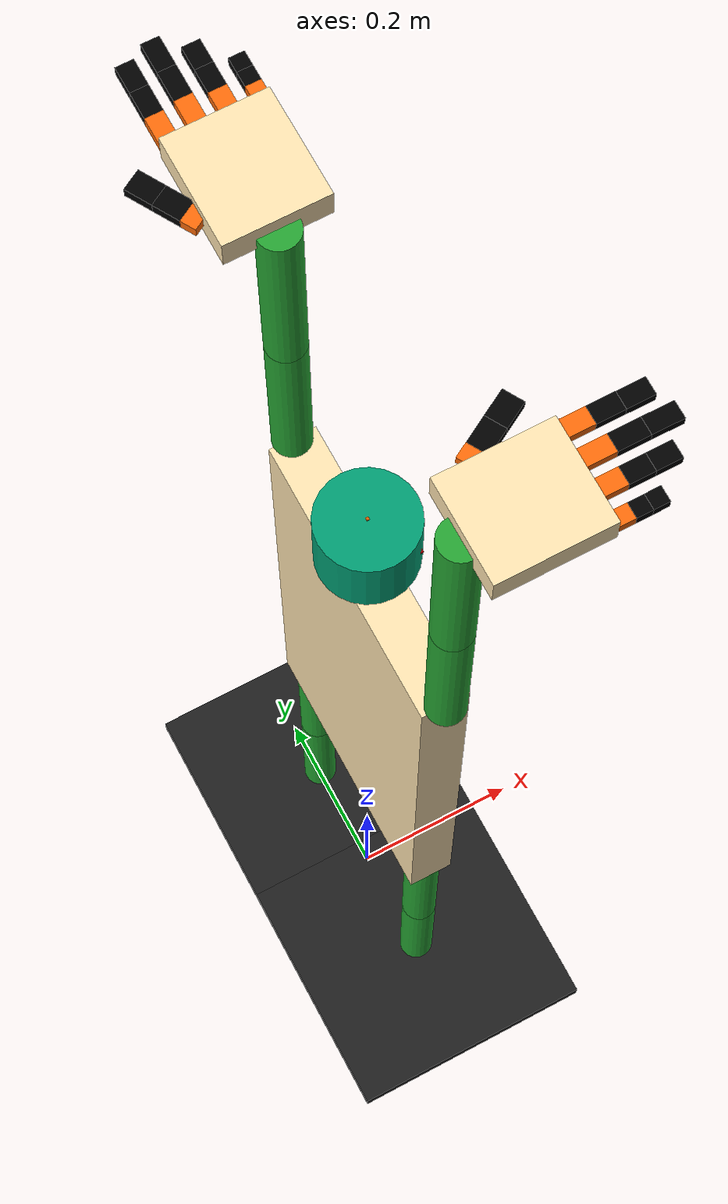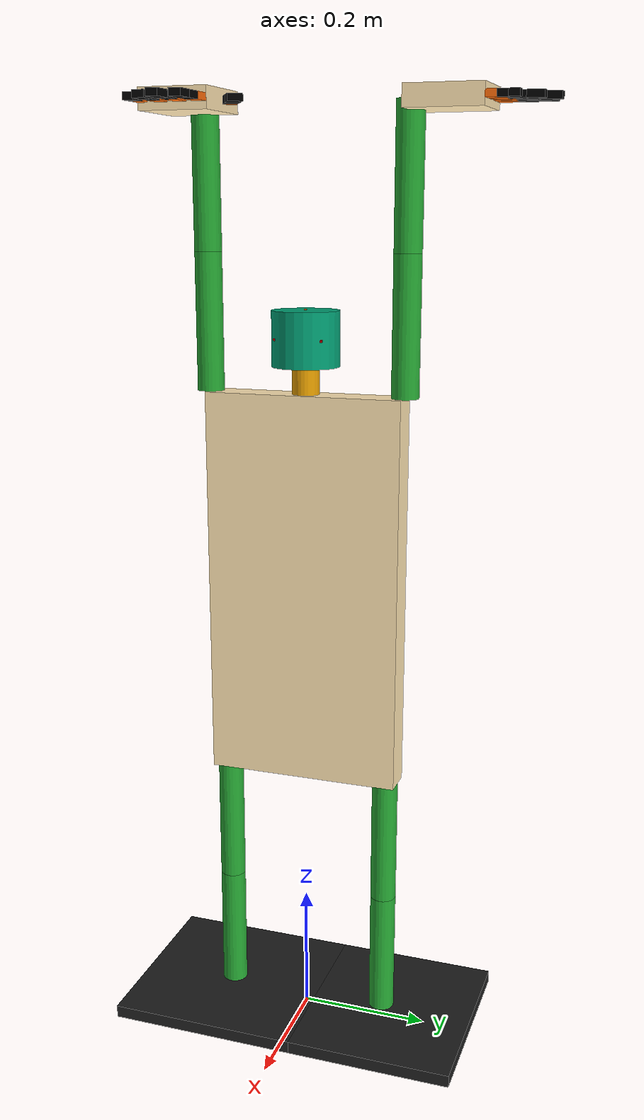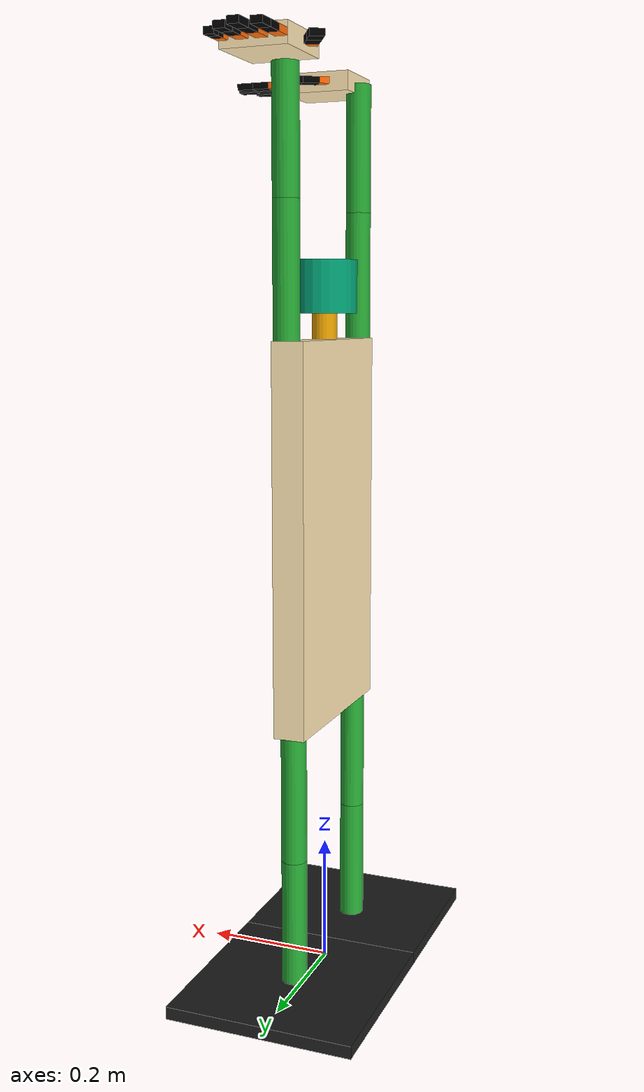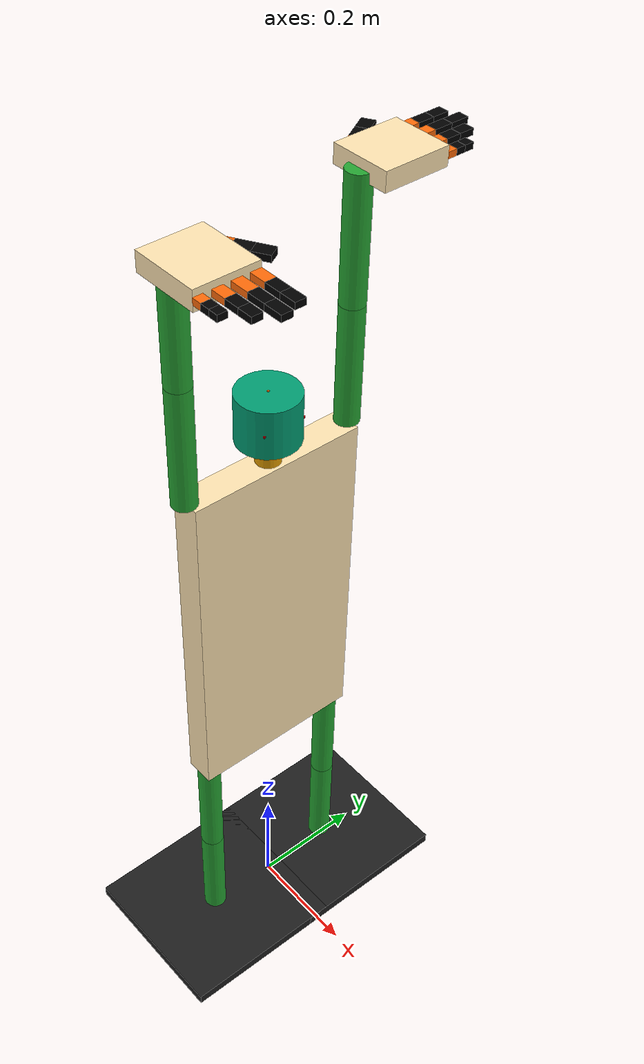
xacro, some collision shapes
<?xml version="1.0"?>

<robot name="baby" xmlns:xacro="http://www.ros.org/wiki/xacro">

  <!-- Constants for robot dimensions -->
  <xacro:property name="PI" value="3.1415926535897931"/>
  <xacro:property name="mass_chest" value="30" />
  <xacro:property name="mass_palm" value="0.8" /> <!-- arbitrary value for mass -->

  <xacro:property name="mass_hand" value="05" /> <!-- arbitrary value for mass -->
  <xacro:property name="mass_neck" value="02" />
  <xacro:property name="mass_leg" value="10" />
  <xacro:property name="mass_foot" value="30" />
  <xacro:property name="mass_dummy" value="2.0" />
  <!-- Total weight=0.2*8+5*2+10*4+2*1+6*1+5*4+0.2*32+25=1.6+10+40+2+6+20+6.4+25 -->
  <xacro:property name="radius" value="0.05" /> <!-- Radii of the cylinder-->
  <xacro:property name="length1" value="0.01" /> <!-- Right_seg42 -->
  <xacro:property name="length2" value="0.02" /> <!-- Rotator -->
  <xacro:property name="width" value="0.01" /> <!-- width of the beam -->

  <xacro:property name="hand_height" value="0.2" /> <!-- little width -->
  <xacro:property name="hand_radius" value="0.020" /> <!-- little width -->

  <xacro:property name="chest_height" value="0.6" />
  <xacro:property name="chest_width" value="0.05" />
  <xacro:property name="chest_length" value="0.3" />

  <xacro:property name="eye_size" value="0.003" />

  <xacro:property name="palm_height" value="0.11" />
  <xacro:property name="palm_length" value="0.1" />
  <xacro:property name="palm_width" value="0.03" />
  <xacro:property name="imr_width" value="0.0173" /> <!-- index middle ring finger width -->
  <xacro:property name="l_width" value="0.015" /> <!-- little finger width -->
  <xacro:property name="x_width" value="0.010" />
  <xacro:property name="thulittle_height" value="0.015" /><!-- thumb and little finger height -->
  <xacro:property name="thuind_height" value="0.0268" /><!-- thumb and index finger height -->
  <xacro:property name="thumb_width" value="0.021" />
  <xacro:property name="middle_height" value="0.03" />
  <xacro:property name="ring_height" value="0.024" />
  <xacro:property name="spacing" value="${(palm_length-imr_width/2-l_width/2)/3}" />

  <xacro:property name="neck_height" value="0.04" />
  <xacro:property name="neck_radius" value="0.02" />

  <xacro:property name="head_height" value="0.08" />
  <xacro:property name="head_radius" value="0.05" />

  <xacro:property name="leg_height" value="0.2" />
  <xacro:property name="leg_radius" value="0.02" />

  <xacro:property name="foot_height" value="0.02" />
  <xacro:property name="foot_length" value="0.3" />
  <xacro:property name="foot_width" value="0.3" />

  <xacro:property name="dummy_size" value="0.10" />
  <xacro:property name="dummy_size_leg" value="0.20" />

  <xacro:include filename="$(find baby_description)/urdf/baby.gazebo" />
  <xacro:include filename="$(find baby_description)/urdf/materials.xacro" />

  <link name="root">
  </link>

  <joint name="dummy" type="fixed">
    <parent link="root"/>
    <child link="Chest"/>
    <origin xyz="0 0 ${leg_height*2+foot_height}" rpy="0 0 0"/>
    <limit effort="1000.0" lower="0" upper="6.20" velocity="10"/>
  </joint>

<!--======================= Chest ========================================= -->

  <link name="Chest">
    <collision>
      <origin xyz="0 0 ${chest_height/2}" rpy="0 0 0"/>
      <geometry>
         <box size="${chest_width} ${chest_length} ${chest_height}"/>
      </geometry>
    </collision>

    <visual>
      <origin xyz="0 0 ${chest_height/2}" rpy="0 0 0"/>
      <geometry>
         <box size="${chest_width} ${chest_length} ${chest_height}"/>
      </geometry>
      <material name="skin"/>
    </visual>

    <inertial>
      <origin xyz="0 0 ${chest_height/2}" rpy="0 0 0"/>
      <mass value="${mass_chest}"/>
      <inertia
          ixx="${mass_chest / 12.0 * (chest_length*chest_length + chest_height*chest_height)}" ixy="0.0" ixz="0.0"
          iyy="${mass_chest / 12.0 * (chest_width*chest_width + chest_height*chest_height)}" iyz="0.0"
          izz="${mass_chest / 12.0 * (chest_width*chest_width + chest_length*chest_length)}"/>
    </inertial>
  </link>

<!--======================Chest Joint=================================== -->

  <joint name="Right_hand_y" type="revolute">
    <parent link="Chest"/>
    <child link="Right_z_handD"/>
    <origin xyz="0 ${chest_length/2} ${chest_height}" rpy="0 0 0"/>
    <axis xyz="0 1 0"/>
    <dynamics damping="0.7"/>
    <limit effort="1000.0" lower="0" upper="6.20" velocity="10"/>
  </joint>

  <joint name="Left_hand_y" type="revolute">
    <parent link="Chest"/>
    <child link="Left_z_handD"/>
    <origin xyz="0 ${-chest_length/2} ${chest_height}" rpy="0 0 0"/>
    <axis xyz="0 1 0"/>
    <dynamics damping="0.7"/>
    <limit effort="1000.0" lower="0" upper="6.20" velocity="10"/>
  </joint>

  <joint name="Neck_y_joint" type="revolute">
    <parent link="Chest"/>
    <child link="Neck"/>
    <origin xyz="0 0 ${chest_height}" rpy="0 0 0"/>
    <axis xyz="0 1 0"/>
    <dynamics damping="0.7"/>
    <limit effort="1000.0" lower="-1.57" upper="1.57" velocity="10"/>
  </joint>

  <joint name="Left_leg_y" type="revolute">
    <parent link="Chest"/>
    <child link="Left_leg_upper"/>
    <origin xyz="0 ${-chest_length/2+leg_radius} 0  " rpy="0 0 0"/>
    <axis xyz="0 1 0"/>
    <dynamics damping="0.7"/>
    <limit effort="1000.0" lower="-1.57" upper="1.57" velocity="10"/>
  </joint>

  <joint name="Right_leg_y" type="revolute">
    <parent link="Chest"/>
    <child link="Right_leg_upper"/>
    <origin xyz="0 ${chest_length/2-leg_radius} 0  " rpy="0 0 0"/>
    <axis xyz="0 1 0"/>
    <dynamics damping="0.7"/>
    <limit effort="1000.0" lower="-1.57" upper="1.57" velocity="10"/>
  </joint>

<!-- ========================3 axis leg joints ========================-->

<!--=======================Left leg ===================================-->

  <link name="Left_leg_upper">
    <collision>
      <origin xyz="0 0 ${-leg_height/2}" rpy="0 0 0"/>
      <geometry>
         <cylinder length ="${leg_height}" radius="${leg_radius}"/>
      </geometry>
    </collision>

    <visual>
      <origin xyz="0 0 ${-leg_height/2}" rpy="0 0 0"/>
      <geometry>
         <cylinder length ="${leg_height}" radius="${leg_radius}"/>
      </geometry>
    </visual>

    <inertial>
      <origin xyz="0 0 ${-leg_height/2}" rpy="0 0 0"/>
      <mass value="${mass_leg}"/>
      <inertia
          ixx="${1/12*mass_leg*leg_height*leg_height}" ixy="0.0" ixz="0.0"
          iyy="${1/12*mass_leg*leg_height*leg_height}" iyz="0.0"
          izz="${mass_leg*leg_radius*leg_radius}"/>
    </inertial>
  </link>

  <joint name="Left_leg_hinge" type="revolute">
    <parent link="Left_leg_upper"/>
    <child link="Left_leg_lower"/>
    <origin xyz="0 0 ${-leg_height}" rpy="0 0 0"/>
    <axis xyz="0 1 0"/>
    <dynamics damping="0.7"/>
    <limit effort="1000.0" lower="-3.14" upper="3.14" velocity="10"/>
  </joint>

  <link name="Left_leg_lower">
    <collision>
      <origin xyz="0 0 ${-leg_height/2}" rpy="0 0 0"/>
      <geometry>
         <cylinder length ="${leg_height}" radius="${leg_radius}"/>
      </geometry>
    </collision>

    <visual>
      <origin xyz="0 0 ${-leg_height/2}" rpy="0 0 0"/>
      <geometry>
         <cylinder length ="${leg_height}" radius="${leg_radius}"/>
      </geometry>
    </visual>

    <inertial>
      <origin xyz="0 0 ${-leg_height/2}" rpy="0 0 0"/>
      <mass value="${mass_leg}"/>
      <inertia
          ixx="${1/12*mass_leg*leg_height*leg_height}" ixy="0.0" ixz="0.0"
          iyy="${1/12*mass_leg*leg_height*leg_height}" iyz="0.0"
          izz="${mass_leg*leg_radius*leg_radius}"/>
    </inertial>
  </link>

  <joint name="Left_foot_y" type="revolute">
    <parent link="Left_leg_lower"/>
    <child link="Left_foot"/>
    <origin xyz="0 0 ${-leg_height}" rpy="0 0 0"/>
    <axis xyz="0 1 0"/>
    <dynamics damping="0.7"/>
    <limit effort="1000.0" lower="-1.57" upper="1.57" velocity="10"/>
  </joint>

  <link name="Left_foot">
    <collision>
      <origin xyz="0 0 ${-foot_height/2}" rpy="0 0 0"/>
      <geometry>
         <box size ="${foot_length} ${foot_width} ${foot_height}"/>
      </geometry>
    </collision>

    <visual>
      <origin xyz="0 0 ${-foot_height/2}" rpy="0 0 0"/>
      <geometry>
         <box size ="${foot_length} ${foot_width} ${foot_height}"/>
      </geometry>
    </visual>

    <inertial>
      <origin xyz="0 0 ${-foot_height/2}" rpy="0 0 0"/>
      <mass value="${mass_foot}"/>
      <inertia
          ixx="${mass_foot/12.0*(foot_length*foot_length+foot_height*foot_height)}" ixy="0.0" ixz="0.0"
          iyy="${mass_foot/12.0*(foot_width*foot_width+foot_height*foot_height)}" iyz="0.0"
          izz="${mass_foot/12.0*(foot_width*foot_width+foot_length*foot_length)}"/>
    </inertial>
  </link>

<!--=======================Right leg ===================================-->

  <link name="Right_leg_upper">
    <collision>
      <origin xyz="0 0 ${-leg_height/2}" rpy="0 0 0"/>
      <geometry>
         <cylinder length ="${leg_height}" radius="${leg_radius}"/>
      </geometry>
    </collision>

    <visual>
      <origin xyz="0 0 ${-leg_height/2}" rpy="0 0 0"/>
      <geometry>
         <cylinder length ="${leg_height}" radius="${leg_radius}"/>
      </geometry>
    </visual>

    <inertial>
      <origin xyz="0 0 ${-leg_height/2}" rpy="0 0 0"/>
      <mass value="${mass_leg}"/>
      <inertia
          ixx="${1/12*mass_leg*leg_height*leg_height}" ixy="0.0" ixz="0.0"
          iyy="${1/12*mass_leg*leg_height*leg_height}" iyz="0.0"
          izz="${mass_leg*leg_radius*leg_radius}"/>
    </inertial>
  </link>

  <joint name="Right_leg_hinge" type="revolute">
    <parent link="Right_leg_upper"/>
    <child link="Right_leg_lower"/>
    <origin xyz="0 0 ${-leg_height}" rpy="0 0 0"/>
    <axis xyz="0 1 0"/>
    <dynamics damping="0.7"/>
    <limit effort="1000.0" lower="-3.14" upper="3.14" velocity="10"/>
  </joint>

  <link name="Right_leg_lower">
    <collision>
      <origin xyz="0 0 ${-leg_height/2}" rpy="0 0 0"/>
      <geometry>
         <cylinder length ="${leg_height}" radius="${leg_radius}"/>
      </geometry>
    </collision>

    <visual>
      <origin xyz="0 0 ${-leg_height/2}" rpy="0 0 0"/>
      <geometry>
         <cylinder length ="${leg_height}" radius="${leg_radius}"/>
      </geometry>
    </visual>

    <inertial>
      <origin xyz="0 0 ${-leg_height/2}" rpy="0 0 0"/>
      <mass value="${mass_leg}"/>
      <inertia
          ixx="${1/12*mass_leg*leg_height*leg_height}" ixy="0.0" ixz="0.0"
          iyy="${1/12*mass_leg*leg_height*leg_height}" iyz="0.0"
          izz="${mass_leg*leg_radius*leg_radius}"/>
    </inertial>
  </link>

  <joint name="Right_foot_y" type="revolute">
    <parent link="Right_leg_lower"/>
    <child link="Right_foot"/>
    <origin xyz="0 0 ${-leg_height}" rpy="0 0 0"/>
    <axis xyz="0 1 0"/>
    <dynamics damping="0.7"/>
    <limit effort="1000.0" lower="-1.57" upper="1.57" velocity="10"/>
  </joint>

  <link name="Right_foot">
    <collision>
      <origin xyz="0 0 ${-foot_height/2}" rpy="0 0 0"/>
      <geometry>
         <box size ="${foot_length} ${foot_width} ${foot_height}"/>
      </geometry>
    </collision>

    <visual>
      <origin xyz="0 0 ${-foot_height/2}" rpy="0 0 0"/>
      <geometry>
         <box size ="${foot_length} ${foot_width} ${foot_height}"/>
      </geometry>
    </visual>

    <inertial>
      <origin xyz="0 0 ${-foot_height/2}" rpy="0 0 0"/>
      <mass value="${mass_foot}"/>
      <inertia
          ixx="${mass_foot/12.0*(foot_length*foot_length+foot_height*foot_height)}" ixy="0.0" ixz="0.0"
          iyy="${mass_foot/12.0*(foot_width*foot_width+foot_height*foot_height)}" iyz="0.0"
          izz="${mass_foot/12.0*(foot_width*foot_width+foot_length*foot_length)}"/>
    </inertial>
  </link>

<!--=======================Neck and Head ===================================-->

  <link name="Neck">
    <collision>
      <origin xyz="0 0 ${neck_height/2}" rpy="0 0 0"/>
      <geometry>
         <cylinder length ="${neck_height}" radius="${neck_radius}"/>
      </geometry>
    </collision>

    <visual>
      <origin xyz="0 0 ${neck_height/2}" rpy="0 0 0"/>
      <geometry>
         <cylinder length ="${neck_height}" radius="${neck_radius}"/>
      </geometry>
    </visual>

    <inertial>
      <origin xyz="0 0 ${neck_height/2}" rpy="0 0 0"/>
      <mass value="${mass_neck}"/>
      <inertia
          ixx="${1/12*mass_neck*neck_height*neck_height}" ixy="0.0" ixz="0.0"
          iyy="${1/12*mass_neck*neck_height*neck_height}" iyz="0.0"
          izz="${mass_neck*neck_radius*neck_radius}"/>
    </inertial>
  </link>

 <joint name="Head_z_joint" type="revolute">
    <parent link="Neck"/>
    <child link="Head_z"/>
    <origin xyz="0 0 ${neck_height}" rpy="0 0 0"/>
    <axis xyz="0 0 1"/>
    <limit effort="1000" velocity="10.0" />
  </joint>

  <link name="Head_z">
    <collision>
      <origin xyz="0 0 ${head_height/20000}" rpy="0 0 0"/>
      <geometry>
         <cylinder length ="${head_height/10000}" radius="${head_radius/10000}"/>
      </geometry>
    </collision>

    <visual>
      <origin xyz="0 0 ${head_height/20000}" rpy="0 0 0"/>
      <geometry>
         <cylinder length ="${head_height/10000}" radius="${head_radius/10000}"/>
      </geometry>
    </visual>

    <inertial>
      <origin xyz="0 0 ${head_height/20000}" rpy="0 0 0"/>
      <mass value="${mass_neck/10000}"/>
      <inertia
          ixx="${1/12*mass_neck/10000*head_height/10000*head_height/10000}" ixy="0.0" ixz="0.0"
          iyy="${1/12*mass_neck/10000*head_height/10000*head_height/10000}" iyz="0.0"
          izz="${mass_neck/10000*head_radius/10000*head_radius/10000}"/>
    </inertial>
  </link>

  <joint name="Head_x_joint" type="revolute">
    <parent link="Neck"/>
    <child link="Head"/>
    <origin xyz="0 0 ${neck_height}" rpy="0 0 0"/>
    <axis xyz="1 0 0"/>
    <limit effort="1000" velocity="1.0" />
  </joint>

  <link name="Head">
    <collision>
      <origin xyz="0 0 ${head_height/2}" rpy="0 0 0"/>
      <geometry>
         <cylinder length ="${head_height}" radius="${head_radius}"/>
      </geometry>
    </collision>

    <visual>
      <origin xyz="0 0 ${head_height/2}" rpy="0 0 0"/>
      <geometry>
         <cylinder length ="${head_height}" radius="${head_radius}"/>
      </geometry>
    </visual>

    <inertial>
      <origin xyz="0 0 ${head_height/2}" rpy="0 0 0"/>
      <mass value="${mass_neck*3}"/>
      <inertia
          ixx="${1/12*mass_neck*3*head_height*head_height}" ixy="0.0" ixz="0.0"
          iyy="${1/12*mass_neck*3*head_height*head_height}" iyz="0.0"
          izz="${mass_neck*3*head_radius*head_radius}"/>
    </inertial>
  </link>

<!--========================= Eyes =====================================-->
  <joint name="Left_eye_joint" type="fixed">
    <axis xyz="0 1 0" />
    <origin xyz="${head_radius/1.414} ${head_radius/1.414} ${head_height/2}" rpy="0 0 0"/>
    <parent link="Head"/>
    <child link="Left_eye"/>
  </joint>
  <joint name="Right_eye_joint" type="fixed">
    <axis xyz="0 1 0" />
    <origin xyz="${head_radius/1.414} ${-head_radius/1.414} ${head_height/2}" rpy="0 0 0"/>
    <parent link="Head"/>
    <child link="Right_eye"/>
  </joint>

  <link name="Left_eye">
    <collision>
      <origin xyz="0 0 0" rpy="0 0 0"/>
      <geometry>
        <box size="${eye_size} ${eye_size} ${eye_size}"/>
      </geometry>
    </collision>

    <visual>
      <origin xyz="0 0 0" rpy="0 0 0"/>
      <geometry>
        <box size="${eye_size} ${eye_size} ${eye_size}"/>
      </geometry>
      <material name="red"/>
    </visual>

    <inertial>
      <mass value="1e-5" />
      <origin xyz="0 0 0" rpy="0 0 0"/>
      <inertia
        ixx="1e-6" ixy="0" ixz="0" iyy="1e-6" iyz="0" izz="1e-6" />
      </inertial>
  </link>
  <link name="Right_eye">
    <collision>
      <origin xyz="0 0 0" rpy="0 0 0"/>
      <geometry>
        <box size="${eye_size} ${eye_size} ${eye_size}"/>
      </geometry>
    </collision>

    <visual>
      <origin xyz="0 0 0" rpy="0 0 0"/>
      <geometry>
        <box size="${eye_size} ${eye_size} ${eye_size}"/>
      </geometry>
      <material name="red"/>
    </visual>

    <inertial>
      <mass value="1e-5" />
      <origin xyz="0 0 0" rpy="0 0 0"/>
      <inertia
        ixx="1e-6" ixy="0" ixz="0" iyy="1e-6" iyz="0" izz="1e-6" />
      </inertial>
  </link>
<!--=======================Scanner=======================================-->
  <joint name="Hokuyo_joint" type="fixed">
    <axis xyz="0 1 0" />
    <origin xyz="0 0 ${head_height}" rpy="0 0 0"/>
    <parent link="Head"/>
    <child link="Hokuyo_link"/>
  </joint>

  <!-- Hokuyo Laser -->
  <link name="Hokuyo_link">
    <collision>
      <origin xyz="0 0 0" rpy="0 0 0"/>
      <geometry>
        <box size="${eye_size} ${eye_size} ${eye_size}"/>
      </geometry>
    </collision>

    <visual>
      <origin xyz="0 0 0" rpy="0 0 0"/>
      <geometry>
        <mesh filename="package://baby_description/meshes/hokuyo.dae"/>
      </geometry>
    </visual>

    <inertial>
      <mass value="1e-5" />
      <origin xyz="0 0 0" rpy="0 0 0"/>
      <inertia ixx="1e-6" ixy="0" ixz="0" iyy="1e-6" iyz="0" izz="1e-6" />
    </inertial>
  </link>
<!--======================= 3 axis Right hand ============================-->

  <link name="Right_z_handD">
    <inertial>
      <origin xyz="0 0 ${dummy_size/2}" rpy="0 0 0"/>
      <mass value="${mass_dummy}"/>
      <inertia
          ixx="${1/12*mass_dummy*dummy_size*dummy_size}" ixy="0.0" ixz="0.0"
          iyy="${1/12*mass_dummy*dummy_size*dummy_size}" iyz="0.0"
          izz="${mass_dummy*hand_radius*hand_radius}"/>
    </inertial>
  </link>

  <joint name="Right_hand_z" type="revolute">
    <parent link="Right_z_handD"/>
    <child link="Right_x_handD"/>
    <origin xyz="0 0 0" rpy="0 0 0"/>
    <axis xyz="0 0 1"/>
    <dynamics damping="0.7"/>
    <limit effort="1000.0" lower="0" upper="6.28" velocity="10"/>
  </joint>

  <link name="Right_x_handD">
    <inertial>
      <origin xyz="0 0 ${dummy_size/2}" rpy="0 0 0"/>
      <mass value="${mass_dummy}"/>
      <inertia
          ixx="${1/12*mass_dummy*dummy_size*dummy_size}" ixy="0.0" ixz="0.0"
          iyy="${1/12*mass_dummy*dummy_size*dummy_size}" iyz="0.0"
          izz="${mass_dummy*hand_radius*hand_radius}"/>
    </inertial>
  </link>

  <joint name="Right_hand_x" type="revolute">
    <parent link="Right_x_handD"/>
    <child link="Right_upper"/>
    <origin xyz="0 0 0" rpy="0 0 0"/>
    <axis xyz="1 0 0"/>
    <dynamics damping="0.7"/>
    <limit effort="1000.0" lower="0" upper="6.28" velocity="10"/>
  </joint>

<!--======================= Right Hand =================================== -->

  <link name="Right_upper">
    <collision>
      <origin xyz="0 0 ${hand_height/2}" rpy="0 0 0"/>
      <geometry>
         <cylinder radius="${hand_radius}" length="${hand_height}"/>
      </geometry>
    </collision>

    <visual>
      <origin xyz="0 0 ${hand_height/2}" rpy="0 0 0"/>
      <geometry>
         <cylinder radius="${hand_radius}" length="${hand_height}"/>
      </geometry>
    </visual>

    <inertial>
      <origin xyz="0 0 ${hand_height/2}" rpy="0 0 0"/>
      <mass value="${mass_hand}"/>
      <inertia
          ixx="${1/12*mass_hand*hand_height*hand_height}" ixy="0.0" ixz="0.0"
          iyy="${1/12*mass_hand*hand_height*hand_height}" iyz="0.0"
          izz="${mass_hand*hand_radius*hand_radius}"/>
    </inertial>
  </link>

  <joint name="Right_hinge" type="revolute">
    <parent link="Right_upper"/>
    <child link="Right_lower"/>
    <origin xyz="${hand_radius/2} 0 ${hand_height}" rpy="0 0 0"/>
    <axis xyz="0 1 0"/>
    <dynamics damping="0.9"/>
    <limit effort="1000.0" lower="0" upper="3.14" velocity="10"/>
  </joint>

  <link name="Right_lower">
     <collision>
      <origin xyz="${-hand_radius/2} 0 ${hand_height/2}" rpy="0 0 0"/>
      <geometry>
         <cylinder radius="${hand_radius}" length="${hand_height}"/>
      </geometry>
    </collision>

    <visual>
      <origin xyz="${-hand_radius/2} 0 ${hand_height/2}" rpy="0 0 0"/>
      <geometry>
         <cylinder radius="${hand_radius}" length="${hand_height}"/>
      </geometry>
    </visual>

    <inertial>
      <origin xyz="${-hand_radius/2} 0 ${hand_height/2}" rpy="0 0 0"/>
      <mass value="${mass_hand}"/>
      <inertia
          ixx="${1/12*mass_hand*hand_height*hand_height}" ixy="0.0" ixz="0.0"
          iyy="${1/12*mass_hand*hand_height*hand_height}" iyz="0.0"
          izz="${mass_hand*hand_radius*hand_radius}"/>
    </inertial>
  </link>

<!-- ===============3 axis PALM joint =======================================
    ===== https://answers.ros.org/question/258420/ball-joint-in-urdf/  -->

   <joint name="Right_palm_y" type="revolute">
    <parent link="Right_lower"/>
    <child link="Right_x_palmD"/>
    <origin xyz="${-hand_radius/2} 0 ${hand_height}" rpy="-1.57 -1.57 0"/>
    <axis xyz="0 1 0"/>
    <dynamics damping="0.7"/>
    <limit effort="1000.0" lower="0" upper="3.14" velocity="10"/>
  </joint>

  <link name="Right_x_palmD">
    <inertial>
      <origin xyz="0 0 ${dummy_size/2}" rpy="0 0 0"/>
      <mass value="${mass_dummy}"/>
      <inertia
          ixx="${1/12*mass_dummy*dummy_size*dummy_size}" ixy="0.0" ixz="0.0"
          iyy="${1/12*mass_dummy*dummy_size*dummy_size}" iyz="0.0"
          izz="${mass_dummy*hand_radius*hand_radius}"/>
    </inertial>
  </link>

  <joint name="Right_palm_x" type="revolute">
    <parent link="Right_x_palmD"/>
    <child link="Right_palm"/>
    <origin xyz="0 0 0" rpy="0 0 0"/>
    <axis xyz="1 0 0"/>
    <dynamics damping="0.7"/>
    <limit effort="1000.0" lower="0" upper="3.14" velocity="10"/>
  </joint>

<!--========================Right_PALM ========================================= -->

 <link name="Right_palm">
    <collision>
      <origin xyz="0 0 ${palm_height/2}" rpy="0 0 0"/>
      <geometry>
         <box size="${palm_width} ${palm_length} ${palm_height}"/>
      </geometry>
    </collision>

    <visual>
      <origin xyz="0 0 ${palm_height/2}" rpy="0 0 0"/>
      <geometry>
         <box size="${palm_width} ${palm_length} ${palm_height}"/>
      </geometry>
      <material name="skin"/>
    </visual>

    <inertial>
      <origin xyz="0 0 ${palm_height/2}" rpy="0 0 0"/>
      <mass value="${mass_palm}"/>
      <inertia
          ixx="${mass_palm/12.0*(palm_length*palm_length+palm_height*palm_height)}" ixy="0.0" ixz="0.0"
          iyy="${mass_palm/12.0*(palm_width*palm_width+palm_height*palm_height)}" iyz="0.0"
          izz="${mass_palm/12.0*(palm_width*palm_width+palm_length*palm_length)}"/>
    </inertial>
  </link>

<!--========================PALM JOINTS ========================================= -->

  <joint name="Right_jointGT" type="fixed">
    <parent link="Right_palm"/>
    <child link="Right_segt1"/>
    <origin xyz="0 ${-palm_length/2} ${0.3*palm_height}" rpy="0.52 0 0"/>
    <axis xyz="0 1 0"/>

  </joint>

  <joint name="Right_jointG1" type="fixed">
    <parent link="Right_palm"/>
    <child link="Right_seg11"/>
    <origin xyz="0 ${-palm_length/2+imr_width/2} ${palm_height}" rpy="0 0 0"/>
    <axis xyz="0 1 0"/>
  </joint>

  <joint name="Right_jointG2" type="fixed">
    <parent link="Right_palm"/>
    <child link="Right_seg21"/>
    <origin xyz="0 ${-palm_length/2+imr_width/2+spacing} ${palm_height}" rpy="0 0 0"/>
    <axis xyz="0 1 0"/>
  </joint>

  <joint name="Right_jointG3" type="fixed">
    <parent link="Right_palm"/>
    <child link="Right_seg31"/>
    <origin xyz="0 ${-palm_length/2+imr_width/2+spacing*2} ${palm_height}" rpy="0 0 0"/>
    <axis xyz="0 1 0"/>
  </joint>

  <joint name="Right_jointG4" type="fixed">
    <parent link="Right_palm"/>
    <child link="Right_seg41"/>
    <origin xyz="0 ${palm_length/2-l_width/2} ${palm_height}" rpy="0 0 0"/>
    <axis xyz="0 1 0"/>
  </joint>

<!--====================== THUMB ===============================-->

  <link name="Right_segt1">
    <collision>
      <origin xyz="0 0 ${thulittle_height/2}" rpy="0 0 0"/>
      <geometry>
         <box size="${x_width} ${thumb_width} ${thulittle_height}"/>
      </geometry>
    </collision>

    <visual>
      <origin xyz="0 0 ${thulittle_height/2}" rpy="0 0 0"/>
      <geometry>
         <box size="${x_width} ${thumb_width} ${thulittle_height}"/>
      </geometry>
      <material name="orange"/>
    </visual>

    <inertial>
      <origin xyz="0 0 ${thulittle_height/2}" rpy="0 0 0"/>
      <mass value="${mass_palm}"/>
      <inertia
    ixx="${mass_palm / 12.0 * (thumb_width*thumb_width + thulittle_height*thulittle_height)}" ixy="0.0" ixz="0.0"
    iyy="${mass_palm / 12.0 * (thulittle_height*thulittle_height + x_width*x_width)}" iyz="0.0"
    izz="${mass_palm / 12.0 * (x_width*x_width + thumb_width*thumb_width)}"/>
    </inertial>
  </link>

  <joint name="Right_jointt1" type="revolute">
    <parent link="Right_segt1"/>
    <child link="Right_segt2"/>
    <origin xyz="${x_width/2} 0 ${thulittle_height}" rpy="0 0 0"/>
    <axis xyz="0 1 0"/>
    <dynamics damping="0.7"/>
    <limit effort="1000.0" lower="0" upper="1.57" velocity="10"/>
  </joint>

  <link name="Right_segt2">
    <collision>
      <origin xyz="${-x_width/2} 0 ${thuind_height/2}" rpy="0 0 0"/>
      <geometry>
         <box size="${x_width} ${thumb_width} ${thuind_height}"/>
      </geometry>
    </collision>

    <visual>
      <origin xyz="${-x_width/2} 0 ${thuind_height/2}" rpy="0 0 0"/>
      <geometry>
         <box size="${x_width} ${thumb_width} ${thuind_height}"/>
      </geometry>
      <material name="black"/>
    </visual>

    <inertial>
      <origin xyz="${-x_width/2} 0 ${thuind_height/2}" rpy="0 0 0"/>
      <mass value="${mass_palm}"/>
      <inertia
    ixx="${mass_palm / 12.0 * (thumb_width*thumb_width + thuind_height*thuind_height)}" ixy="0.0" ixz="0.0"
    iyy="${mass_palm / 12.0 * (thuind_height*thuind_height + x_width*x_width)}" iyz="0.0"
    izz="${mass_palm / 12.0 * (x_width*x_width + thumb_width*thumb_width)}"/>
    </inertial>
  </link>

  <joint name="Right_jointt2" type="revolute">
    <parent link="Right_segt2"/>
    <child link="Right_segt3"/>
    <origin xyz="0 0 ${thuind_height}" rpy="0 0 0"/>
    <axis xyz="0 1 0"/>
    <dynamics damping="0.7"/>
    <limit effort="1000.0" lower="0" upper="1.57" velocity="10"/>
  </joint>

  <link name="Right_segt3">
    <collision>
      <origin xyz="${-x_width/2} 0 ${thuind_height/2}" rpy="0 0 0"/>
      <geometry>
         <box size="${x_width} ${thumb_width} ${thuind_height}"/>
      </geometry>
    </collision>

    <visual>
      <origin xyz="${-x_width/2} 0 ${thuind_height/2}" rpy="0 0 0"/>
      <geometry>
         <box size="${x_width} ${thumb_width} ${thuind_height}"/>
      </geometry>
      <material name="black"/>
    </visual>

    <inertial>
      <origin xyz="${-x_width/2} 0 ${thuind_height/2}" rpy="0 0 0"/>
      <mass value="${mass_palm}"/>
      <inertia
    ixx="${mass_palm / 12.0 * (thumb_width*thumb_width + thuind_height*thuind_height)}" ixy="0.0" ixz="0.0"
    iyy="${mass_palm / 12.0 * (thuind_height*thuind_height + x_width*x_width)}" iyz="0.0"
    izz="${mass_palm / 12.0 * (x_width*x_width + thumb_width*thumb_width)}"/>
    </inertial>
  </link>

<!--====================== INDEX FINGER ===============================-->

  <link name="Right_seg11">
    <collision>
      <origin xyz="0 0 ${thuind_height/2}" rpy="0 0 0"/>
      <geometry>
	       <box size="${x_width} ${imr_width} ${thuind_height}"/>
      </geometry>
    </collision>

    <visual>
      <origin xyz="0 0 ${thuind_height/2}" rpy="0 0 0"/>
      <geometry>
	       <box size="${x_width} ${imr_width} ${thuind_height}"/>
      </geometry>
      <material name="orange"/>
    </visual>

    <inertial>
      <origin xyz="0 0 ${thuind_height/2}" rpy="0 0 0"/>
      <mass value="${mass_palm}"/>
      <inertia
	  ixx="${mass_palm / 12.0 * (length1*length1 + length1*length1)}" ixy="0.0" ixz="0.0"
	  iyy="${mass_palm / 12.0 * (length1*length1 + length1*length1)}" iyz="0.0"
	  izz="${mass_palm / 12.0 * (length1*length1 + length1*length1)}"/>
    </inertial>
  </link>

  <joint name="Right_joint11" type="revolute">
    <parent link="Right_seg11"/>
    <child link="Right_seg12"/>
    <origin xyz="${x_width/2} 0 ${thuind_height}" rpy="0 0 0"/>
    <axis xyz="0 1 0"/>
    <dynamics damping="0.7"/>
    <limit effort="1000.0" lower="0" upper="1.57" velocity="10"/>
  </joint>

  <link name="Right_seg12">
    <collision>
      <origin xyz="${-x_width/2} 0 ${thuind_height/2}" rpy="0 0 0"/>
      <geometry>
	       <box size="${x_width} ${imr_width} ${thuind_height}"/>
      </geometry>
    </collision>

    <visual>
      <origin xyz="${-x_width/2} 0 ${thuind_height/2}" rpy="0 0 0"/>
      <geometry>
	       <box size="${x_width} ${imr_width} ${thuind_height}"/>
      </geometry>
      <material name="black"/>
    </visual>

    <inertial>
      <origin xyz="${-x_width/2} 0 ${thuind_height/2}" rpy="0 0 0"/>
      <mass value="${mass_palm}"/>
      <inertia
	  ixx="${mass_palm / 12.0 * (width*width + width*width)}" ixy="0.0" ixz="0.0"
	  iyy="${mass_palm / 12.0 * (length2*length2 + width*width)}" iyz="0.0"
	  izz="${mass_palm / 12.0 * (width*width + length2*length2)}"/>
    </inertial>
  </link>

  <joint name="Right_joint12" type="revolute">
    <parent link="Right_seg12"/>
    <child link="Right_seg13"/>
    <origin xyz="0 0 ${thuind_height}" rpy="0 0 0"/>
    <axis xyz="0 1 0"/>
    <dynamics damping="0.7"/>
    <limit effort="1000.0" lower="0" upper="1.57" velocity="10"/>
  </joint>

  <link name="Right_seg13">
    <collision>
      <origin xyz="${-x_width/2} 0 ${thuind_height/2}" rpy="0 0 0"/>
      <geometry>
         <box size="${x_width} ${imr_width} ${thuind_height}"/>
      </geometry>
    </collision>

    <visual>
      <origin xyz="${-x_width/2} 0 ${thuind_height/2}" rpy="0 0 0"/>
      <geometry>
         <box size="${x_width} ${imr_width} ${thuind_height}"/>
      </geometry>
      <material name="black"/>
    </visual>

    <inertial>
      <origin xyz="${-x_width/2} 0 ${thuind_height/2}" rpy="0 0 0"/>
      <mass value="${mass_palm}"/>
      <inertia
    ixx="${mass_palm / 12.0 * (width*width + width*width)}" ixy="0.0" ixz="0.0"
    iyy="${mass_palm / 12.0 * (length2*length2 + width*width)}" iyz="0.0"
    izz="${mass_palm / 12.0 * (width*width + length2*length2)}"/>
    </inertial>
  </link>

<!--====================== MIDDLE FINGER ===============================-->

  <link name="Right_seg21">
    <collision>
      <origin xyz="0 0 ${middle_height/2}" rpy="0 0 0"/>
      <geometry>
         <box size="${x_width} ${imr_width} 0.2"/>
      </geometry>
    </collision>

    <visual>
      <origin xyz="0 0 ${middle_height/2}" rpy="0 0 0"/>
      <geometry>
         <box size="${x_width} ${imr_width} ${middle_height}"/>
      </geometry>
      <material name="orange"/>
    </visual>

    <inertial>
      <origin xyz="0 0 ${middle_height/2}" rpy="0 0 0"/>
      <mass value="${mass_palm}"/>
      <inertia
    ixx="${mass_palm / 12.0 * (length1*length1 + length1*length1)}" ixy="0.0" ixz="0.0"
    iyy="${mass_palm / 12.0 * (length1*length1 + length1*length1)}" iyz="0.0"
    izz="${mass_palm / 12.0 * (length1*length1 + length1*length1)}"/>
    </inertial>
  </link>

  <joint name="Right_joint21" type="revolute">
    <parent link="Right_seg21"/>
    <child link="Right_seg22"/>
    <origin xyz="${x_width/2} 0.0 ${middle_height}" rpy="0 0 0"/>
    <axis xyz="0 1 0"/>
    <dynamics damping="0.7"/>
    <limit effort="1000.0" lower="0" upper="1.57" velocity="10"/>
  </joint>

  <link name="Right_seg22">
    <collision>
      <origin xyz="${-x_width/2} 0 ${middle_height/2}" rpy="0 0 0"/>
      <geometry>
         <box size="${x_width} ${imr_width} ${middle_height}"/>
      </geometry>
    </collision>

    <visual>
      <origin xyz="${-x_width/2} 0 ${middle_height/2}" rpy="0 0 0"/>
      <geometry>
         <box size="${x_width} ${imr_width} ${middle_height}"/>
      </geometry>
      <material name="black"/>
    </visual>

    <inertial>
      <origin xyz="${-x_width/2} 0 ${middle_height/2}" rpy="0 0 0"/>
      <mass value="${mass_palm}"/>
      <inertia
    ixx="${mass_palm / 12.0 * (width*width + width*width)}" ixy="0.0" ixz="0.0"
    iyy="${mass_palm / 12.0 * (length2*length2 + width*width)}" iyz="0.0"
    izz="${mass_palm / 12.0 * (width*width + length2*length2)}"/>
    </inertial>
  </link>

  <joint name="Right_joint22" type="revolute">
    <parent link="Right_seg22"/>
    <child link="Right_seg23"/>
    <origin xyz="0 0 ${middle_height}" rpy="0 0 0"/>
    <axis xyz="0 1 0"/>
    <dynamics damping="0.7"/>
    <limit effort="1000.0" lower="0" upper="1.57" velocity="10"/>
  </joint>

  <link name="Right_seg23">
    <collision>
      <origin xyz="${-x_width/2} 0 ${middle_height/2}" rpy="0 0 0"/>
      <geometry>
         <box size="${x_width} ${imr_width} ${middle_height}"/>
      </geometry>
    </collision>

    <visual>
      <origin xyz="${-x_width/2} 0 ${middle_height/2}" rpy="0 0 0"/>
      <geometry>
         <box size="${x_width} ${imr_width} ${middle_height}"/>
      </geometry>
      <material name="black"/>
    </visual>

    <inertial>
      <origin xyz="${-x_width/2} 0 ${middle_height/2}" rpy="0 0 0"/>
      <mass value="${mass_palm}"/>
      <inertia
    ixx="${mass_palm / 12.0 * (width*width + width*width)}" ixy="0.0" ixz="0.0"
    iyy="${mass_palm / 12.0 * (length2*length2 + width*width)}" iyz="0.0"
    izz="${mass_palm / 12.0 * (width*width + length2*length2)}"/>
    </inertial>
  </link>

<!--====================== RING FINGER ===============================-->

  <link name="Right_seg31">
    <collision>
      <origin xyz="0 0 ${ring_height/2}" rpy="0 0 0"/>
      <geometry>
         <box size="${x_width} ${imr_width} ${ring_height}"/>
      </geometry>
    </collision>

    <visual>
      <origin xyz="0 0 ${ring_height/2}" rpy="0 0 0"/>
      <geometry>
         <box size="${x_width} ${imr_width} ${ring_height}"/>
      </geometry>
      <material name="orange"/>
    </visual>

    <inertial>
      <origin xyz="0 0 ${ring_height/2}" rpy="0 0 0"/>
      <mass value="${mass_palm}"/>
      <inertia
    ixx="${mass_palm / 12.0 * (length1*length1 + length1*length1)}" ixy="0.0" ixz="0.0"
    iyy="${mass_palm / 12.0 * (length1*length1 + length1*length1)}" iyz="0.0"
    izz="${mass_palm / 12.0 * (length1*length1 + length1*length1)}"/>
    </inertial>
  </link>

  <joint name="Right_joint31" type="revolute">
    <parent link="Right_seg31"/>
    <child link="Right_seg32"/>
    <origin xyz="${x_width/2} 0.0 ${ring_height}" rpy="0 0 0"/>
    <axis xyz="0 1 0"/>
    <dynamics damping="0.7"/>
    <limit effort="1000.0" lower="0" upper="1.57" velocity="10"/>
  </joint>

  <link name="Right_seg32">
    <collision>
      <origin xyz="${-x_width/2} 0 ${ring_height/2}" rpy="0 0 0"/>
      <geometry>
         <box size="${x_width} ${imr_width} ${ring_height}"/>
      </geometry>
    </collision>

    <visual>
      <origin xyz="${-x_width/2} 0 ${ring_height/2}" rpy="0 0 0"/>
      <geometry>
         <box size="${x_width} ${imr_width} ${ring_height}"/>
      </geometry>
      <material name="black"/>
    </visual>

    <inertial>
      <origin xyz="${-x_width/2} 0 ${ring_height/2}" rpy="0 0 0"/>
      <mass value="${mass_palm}"/>
      <inertia
    ixx="${mass_palm / 12.0 * (width*width + width*width)}" ixy="0.0" ixz="0.0"
    iyy="${mass_palm / 12.0 * (length2*length2 + width*width)}" iyz="0.0"
    izz="${mass_palm / 12.0 * (width*width + length2*length2)}"/>
    </inertial>
  </link>

  <joint name="Right_joint32" type="revolute">
    <parent link="Right_seg32"/>
    <child link="Right_seg33"/>
    <origin xyz="0 0 ${ring_height}" rpy="0 0 0"/>
    <axis xyz="0 1 0"/>
    <dynamics damping="0.7"/>
    <limit effort="1000.0" lower="0" upper="1.57" velocity="10"/>
  </joint>

  <link name="Right_seg33">
    <collision>
      <origin xyz="${-x_width/2} 0 ${ring_height/2}" rpy="0 0 0"/>
      <geometry>
         <box size="${x_width} ${imr_width} ${ring_height}"/>
      </geometry>
    </collision>

    <visual>
      <origin xyz="${-x_width/2} 0 ${ring_height/2}" rpy="0 0 0"/>
      <geometry>
         <box size="${x_width} ${imr_width} ${ring_height}"/>
      </geometry>
      <material name="black"/>
    </visual>

    <inertial>
      <origin xyz="${-x_width/2} 0 ${ring_height/2}" rpy="0 0 0"/>
      <mass value="${mass_palm}"/>
      <inertia
    ixx="${mass_palm / 12.0 * (width*width + width*width)}" ixy="0.0" ixz="0.0"
    iyy="${mass_palm / 12.0 * (length2*length2 + width*width)}" iyz="0.0"
    izz="${mass_palm / 12.0 * (width*width + length2*length2)}"/>
    </inertial>
  </link>

<!--====================== LITTLE FINGER ===============================-->

  <link name="Right_seg41">
    <collision>
      <origin xyz="0 0 ${thulittle_height/2}" rpy="0 0 0"/>
      <geometry>
         <box size="${x_width} ${l_width} ${thulittle_height}"/>
      </geometry>
    </collision>

    <visual>
      <origin xyz="0 0 ${thulittle_height/2}" rpy="0 0 0"/>
      <geometry>
         <box size="${x_width} ${l_width} ${thulittle_height}"/>
      </geometry>
      <material name="orange"/>
    </visual>

    <inertial>
      <origin xyz="0 0 ${thulittle_height/2}" rpy="0 0 0"/>
      <mass value="${mass_palm}"/>
      <inertia
    ixx="${mass_palm / 12.0 * (length1*length1 + length1*length1)}" ixy="0.0" ixz="0.0"
    iyy="${mass_palm / 12.0 * (length1*length1 + length1*length1)}" iyz="0.0"
    izz="${mass_palm / 12.0 * (length1*length1 + length1*length1)}"/>
    </inertial>
  </link>

  <joint name="Right_joint41" type="revolute">
    <parent link="Right_seg41"/>
    <child link="Right_seg42"/>
    <origin xyz="${x_width/2} 0.0 ${thulittle_height}" rpy="0 0 0"/>
    <axis xyz="0 1 0"/>
    <dynamics damping="0.7"/>
    <limit effort="1000.0" lower="0" upper="1.57" velocity="10"/>
  </joint>

  <link name="Right_seg42">
    <collision>
      <origin xyz="${-x_width/2} 0 ${thulittle_height/2}" rpy="0 0 0"/>
      <geometry>
         <box size="${x_width} ${l_width} ${thulittle_height}"/>
      </geometry>
    </collision>

    <visual>
      <origin xyz="${-x_width/2} 0 ${thulittle_height/2}" rpy="0 0 0"/>
      <geometry>
         <box size="${x_width} ${l_width} ${thulittle_height}"/>
      </geometry>
      <material name="black"/>
    </visual>

    <inertial>
      <origin xyz="${-x_width/2} 0 ${thulittle_height/2}" rpy="0 0 0"/>
      <mass value="${mass_palm}"/>
      <inertia
    ixx="${mass_palm / 12.0 * (width*width + width*width)}" ixy="0.0" ixz="0.0"
    iyy="${mass_palm / 12.0 * (length2*length2 + width*width)}" iyz="0.0"
    izz="${mass_palm / 12.0 * (width*width + length2*length2)}"/>
    </inertial>
  </link>

  <joint name="Right_joint42" type="revolute">
    <parent link="Right_seg42"/>
    <child link="Right_seg43"/>
    <origin xyz="0 0 ${thulittle_height}" rpy="0 0 0"/>
    <axis xyz="0 1 0"/>
    <dynamics damping="0.7"/>
    <limit effort="1000.0" lower="0" upper="1.57" velocity="10"/>
  </joint>

  <link name="Right_seg43">
    <collision>
      <origin xyz="${-x_width/2} 0 ${thulittle_height/2}" rpy="0 0 0"/>
      <geometry>
         <box size="${x_width} ${l_width} ${thulittle_height}"/>
      </geometry>
    </collision>

    <visual>
      <origin xyz="${-x_width/2} 0 ${thulittle_height/2}" rpy="0 0 0"/>
      <geometry>
         <box size="${x_width} ${l_width} ${thulittle_height}"/>
      </geometry>
      <material name="black"/>
    </visual>

    <inertial>
      <origin xyz="${-x_width/2} 0 ${thulittle_height/2}" rpy="0 0 0"/>
      <mass value="${mass_palm}"/>
      <inertia
    ixx="${mass_palm / 12.0 * (width*width + width*width)}" ixy="0.0" ixz="0.0"
    iyy="${mass_palm / 12.0 * (length2*length2 + width*width)}" iyz="0.0"
    izz="${mass_palm / 12.0 * (width*width + length2*length2)}"/>
    </inertial>
  </link>
<!-- ========================3 axis left hand joint ======================-->
<link name="Left_z_handD">
    <inertial>
      <origin xyz="0 0 ${dummy_size/2}" rpy="0 0 0"/>
      <mass value="${mass_dummy}"/>
      <inertia
          ixx="${1/12*mass_dummy*dummy_size*dummy_size}" ixy="0.0" ixz="0.0"
          iyy="${1/12*mass_dummy*dummy_size*dummy_size}" iyz="0.0"
          izz="${mass_dummy*hand_radius*hand_radius}"/>
    </inertial>
  </link>

  <joint name="Left_hand_z" type="revolute">
    <parent link="Left_z_handD"/>
    <child link="Left_x_handD"/>
    <origin xyz="0 0 0" rpy="0 0 0"/>
    <axis xyz="0 0 1"/>
    <dynamics damping="0.7"/>
    <limit effort="1000.0" lower="0" upper="6.28" velocity="10"/>
  </joint>

  <link name="Left_x_handD">
    <inertial>
      <origin xyz="0 0 ${dummy_size/2}" rpy="0 0 0"/>
      <mass value="${mass_dummy}"/>
      <inertia
          ixx="${1/12*mass_dummy*dummy_size*dummy_size}" ixy="0.0" ixz="0.0"
          iyy="${1/12*mass_dummy*dummy_size*dummy_size}" iyz="0.0"
          izz="${mass_dummy*hand_radius*hand_radius}"/>
    </inertial>
  </link>

  <joint name="Left_hand_x" type="revolute">
    <parent link="Left_x_handD"/>
    <child link="Left_upper"/>
    <origin xyz="0 0 0" rpy="0 0 0"/>
    <axis xyz="1 0 0"/>
    <dynamics damping="0.7"/>
    <limit effort="1000.0" lower="0" upper="6.28" velocity="10"/>
  </joint>

<!--======================= Left Hand =================================== -->

  <link name="Left_upper">
    <collision>
      <origin xyz="0 0 ${hand_height/2}" rpy="0 0 0"/>
      <geometry>
         <cylinder radius="${hand_radius}" length="${hand_height}"/>
      </geometry>
    </collision>

    <visual>
      <origin xyz="0 0 ${hand_height/2}" rpy="0 0 0"/>
      <geometry>
         <cylinder radius="${hand_radius}" length="${hand_height}"/>
      </geometry>
    </visual>

    <inertial>
      <origin xyz="0 0 ${hand_height/2}" rpy="0 0 0"/>
      <mass value="${mass_hand}"/>
      <inertia
          ixx="${1/12*mass_hand*hand_height*hand_height}" ixy="0.0" ixz="0.0"
          iyy="${1/12*mass_hand*hand_height*hand_height}" iyz="0.0"
          izz="${mass_hand*hand_radius*hand_radius}"/>
    </inertial>
  </link>

  <joint name="Left_hinge" type="revolute">
    <parent link="Left_upper"/>
    <child link="Left_lower"/>
    <origin xyz="${hand_radius/2} 0 ${hand_height}" rpy="0 0 0"/>
    <axis xyz="0 1 0"/>
    <dynamics damping="0.9"/>
    <limit effort="1000.0" lower="0" upper="3.14" velocity="10"/>
  </joint>

  <link name="Left_lower">
     <collision>
      <origin xyz="${-hand_radius/2} 0 ${hand_height/2}" rpy="0 0 0"/>
      <geometry>
         <cylinder radius="${hand_radius}" length="${hand_height}"/>
      </geometry>
    </collision>

    <visual>
      <origin xyz="${-hand_radius/2} 0 ${hand_height/2}" rpy="0 0 0"/>
      <geometry>
         <cylinder radius="${hand_radius}" length="${hand_height}"/>
      </geometry>
    </visual>

    <inertial>
      <origin xyz="${-hand_radius/2} 0 ${hand_height/2}" rpy="0 0 0"/>
      <mass value="${mass_hand}"/>
      <inertia
          ixx="${1/12*mass_hand*hand_height*hand_height}" ixy="0.0" ixz="0.0"
          iyy="${1/12*mass_hand*hand_height*hand_height}" iyz="0.0"
          izz="${mass_hand*hand_radius*hand_radius}"/>
    </inertial>
  </link>

<!-- ===============3 axis PALM joint =======================================
    ===== https://answers.ros.org/question/258420/ball-joint-in-urdf/  -->

   <joint name="Left_palm_y" type="revolute">
    <parent link="Left_lower"/>
    <child link="Left_z_palmD"/>
    <origin xyz="${-hand_radius/2} 0 ${hand_height}" rpy="0 -1.57 3.14"/>
    <axis xyz="0 1 0"/>
    <dynamics damping="0.7"/>
    <limit effort="1000.0" lower="0" upper="3.14" velocity="10"/>
  </joint>

  <link name="Left_z_palmD">
    <inertial>
      <origin xyz="0 0 ${dummy_size/2}" rpy="0 0 0"/>
      <mass value="${mass_dummy}"/>
      <inertia
          ixx="${1/12*mass_dummy*dummy_size*dummy_size}" ixy="0.0" ixz="0.0"
          iyy="${1/12*mass_dummy*dummy_size*dummy_size}" iyz="0.0"
          izz="${mass_dummy*hand_radius*hand_radius}"/>
    </inertial>
  </link>

  <joint name="Left_palm_z" type="revolute">
    <parent link="Left_z_palmD"/>
    <child link="Left_x_palmD"/>
    <origin xyz="0 0 0" rpy="0 0 0"/>
    <axis xyz="0 0 1"/>
    <dynamics damping="0.7"/>
    <limit effort="1000.0" lower="0" upper="6.28" velocity="10"/>
  </joint>

  <link name="Left_x_palmD">
    <inertial>
      <origin xyz="0 0 ${dummy_size/2}" rpy="0 0 0"/>
      <mass value="${mass_dummy}"/>
      <inertia
          ixx="${1/12*mass_dummy*dummy_size*dummy_size}" ixy="0.0" ixz="0.0"
          iyy="${1/12*mass_dummy*dummy_size*dummy_size}" iyz="0.0"
          izz="${mass_dummy*hand_radius*hand_radius}"/>
    </inertial>
  </link>

  <joint name="Left_palm_x" type="revolute">
    <parent link="Left_x_palmD"/>
    <child link="Left_palm"/>
    <origin xyz="0 0 0" rpy="0 0 0"/>
    <axis xyz="1 0 0"/>
    <dynamics damping="0.7"/>
    <limit effort="1000.0" lower="0" upper="3.14" velocity="10"/>
  </joint>

<!--========================Left_PALM ========================================= -->

 <link name="Left_palm">
    <collision>
      <origin xyz="0 0 ${palm_height/2}" rpy="0 0 0"/>
      <geometry>
         <box size="${palm_width} ${palm_length} ${palm_height}"/>
      </geometry>
    </collision>

    <visual>
      <origin xyz="0 0 ${palm_height/2}" rpy="0 0 0"/>
      <geometry>
         <box size="${palm_width} ${palm_length} ${palm_height}"/>
      </geometry>
      <material name="skin"/>
    </visual>

    <inertial>
      <origin xyz="0 0 ${palm_height/2}" rpy="0 0 0"/>
      <mass value="${mass_palm}"/>
      <inertia
          ixx="${mass_palm/12.0*(palm_length*palm_length+palm_height*palm_height)}" ixy="0.0" ixz="0.0"
          iyy="${mass_palm/12.0*(palm_width*palm_width+palm_height*palm_height)}" iyz="0.0"
          izz="${mass_palm/12.0*(palm_width*palm_width+palm_length*palm_length)}"/>
    </inertial>
  </link>

<!--========================PALM JOINTS ========================================= -->

  <joint name="Left_jointGT" type="fixed">
    <parent link="Left_palm"/>
    <child link="Left_segt1"/>
    <origin xyz="0 ${-palm_length/2} ${0.3*palm_height}" rpy="0.52 0 0"/>
    <axis xyz="0 1 0"/>

  </joint>

  <joint name="Left_jointG1" type="fixed">
    <parent link="Left_palm"/>
    <child link="Left_seg11"/>
    <origin xyz="0 ${-palm_length/2+imr_width/2} ${palm_height}" rpy="0 0 0"/>
    <axis xyz="0 1 0"/>
  </joint>

  <joint name="Left_jointG2" type="fixed">
    <parent link="Left_palm"/>
    <child link="Left_seg21"/>
    <origin xyz="0 ${-palm_length/2+imr_width/2+spacing} ${palm_height}" rpy="0 0 0"/>
    <axis xyz="0 1 0"/>
  </joint>

  <joint name="Left_jointG3" type="fixed">
    <parent link="Left_palm"/>
    <child link="Left_seg31"/>
    <origin xyz="0 ${-palm_length/2+imr_width/2+spacing*2} ${palm_height}" rpy="0 0 0"/>
    <axis xyz="0 1 0"/>
  </joint>

  <joint name="Left_jointG4" type="fixed">
    <parent link="Left_palm"/>
    <child link="Left_seg41"/>
    <origin xyz="0 ${palm_length/2-l_width/2} ${palm_height}" rpy="0 0 0"/>
    <axis xyz="0 1 0"/>
  </joint>

<!--====================== THUMB ===============================-->

  <link name="Left_segt1">
    <collision>
      <origin xyz="0 0 ${thulittle_height/2}" rpy="0 0 0"/>
      <geometry>
         <box size="${x_width} ${thumb_width} ${thulittle_height}"/>
      </geometry>
    </collision>

    <visual>
      <origin xyz="0 0 ${thulittle_height/2}" rpy="0 0 0"/>
      <geometry>
         <box size="${x_width} ${thumb_width} ${thulittle_height}"/>
      </geometry>
      <material name="orange"/>
    </visual>

    <inertial>
      <origin xyz="0 0 ${thulittle_height/2}" rpy="0 0 0"/>
      <mass value="${mass_palm}"/>
      <inertia
    ixx="${mass_palm / 12.0 * (length1*length1 + length1*length1)}" ixy="0.0" ixz="0.0"
    iyy="${mass_palm / 12.0 * (length1*length1 + length1*length1)}" iyz="0.0"
    izz="${mass_palm / 12.0 * (length1*length1 + length1*length1)}"/>
    </inertial>
  </link>

  <joint name="Left_jointt1" type="revolute">
    <parent link="Left_segt1"/>
    <child link="Left_segt2"/>
    <origin xyz="${x_width/2} 0 ${thulittle_height}" rpy="0 0 0"/>
    <axis xyz="0 1 0"/>
    <dynamics damping="0.7"/>
    <limit effort="1000.0" lower="0" upper="1.57" velocity="10"/>
  </joint>

  <link name="Left_segt2">
    <collision>
      <origin xyz="${-x_width/2} 0 ${thuind_height/2}" rpy="0 0 0"/>
      <geometry>
         <box size="${x_width} ${thumb_width} ${thuind_height}"/>
      </geometry>
    </collision>

    <visual>
      <origin xyz="${-x_width/2} 0 ${thuind_height/2}" rpy="0 0 0"/>
      <geometry>
         <box size="${x_width} ${thumb_width} ${thuind_height}"/>
      </geometry>
      <material name="black"/>
    </visual>

    <inertial>
      <origin xyz="${-x_width/2} 0 ${thuind_height/2}" rpy="0 0 0"/>
      <mass value="${mass_palm}"/>
      <inertia
    ixx="${mass_palm / 12.0 * (width*width + width*width)}" ixy="0.0" ixz="0.0"
    iyy="${mass_palm / 12.0 * (length2*length2 + width*width)}" iyz="0.0"
    izz="${mass_palm / 12.0 * (width*width + length2*length2)}"/>
    </inertial>
  </link>

  <joint name="Left_jointt2" type="revolute">
    <parent link="Left_segt2"/>
    <child link="Left_segt3"/>
    <origin xyz="0 0 ${thuind_height}" rpy="0 0 0"/>
    <axis xyz="0 1 0"/>
    <dynamics damping="0.7"/>
    <limit effort="1000.0" lower="0" upper="1.57" velocity="10"/>
  </joint>

  <link name="Left_segt3">
    <collision>
      <origin xyz="${-x_width/2} 0 ${thuind_height/2}" rpy="0 0 0"/>
      <geometry>
         <box size="${x_width} ${thumb_width} ${thuind_height}"/>
      </geometry>
    </collision>

    <visual>
      <origin xyz="${-x_width/2} 0 ${thuind_height/2}" rpy="0 0 0"/>
      <geometry>
         <box size="${x_width} ${thumb_width} ${thuind_height}"/>
      </geometry>
      <material name="black"/>
    </visual>

    <inertial>
      <origin xyz="${-x_width/2} 0 ${thuind_height/2}" rpy="0 0 0"/>
      <mass value="${mass_palm}"/>
      <inertia
    ixx="${mass_palm / 12.0 * (width*width + width*width)}" ixy="0.0" ixz="0.0"
    iyy="${mass_palm / 12.0 * (length2*length2 + width*width)}" iyz="0.0"
    izz="${mass_palm / 12.0 * (width*width + length2*length2)}"/>
    </inertial>
  </link>

<!--====================== INDEX FINGER ===============================-->

  <link name="Left_seg11">
    <collision>
      <origin xyz="0 0 ${thuind_height/2}" rpy="0 0 0"/>
      <geometry>
         <box size="${x_width} ${imr_width} ${thuind_height}"/>
      </geometry>
    </collision>

    <visual>
      <origin xyz="0 0 ${thuind_height/2}" rpy="0 0 0"/>
      <geometry>
         <box size="${x_width} ${imr_width} ${thuind_height}"/>
      </geometry>
      <material name="orange"/>
    </visual>

    <inertial>
      <origin xyz="0 0 ${thuind_height/2}" rpy="0 0 0"/>
      <mass value="${mass_palm}"/>
      <inertia
    ixx="${mass_palm / 12.0 * (length1*length1 + length1*length1)}" ixy="0.0" ixz="0.0"
    iyy="${mass_palm / 12.0 * (length1*length1 + length1*length1)}" iyz="0.0"
    izz="${mass_palm / 12.0 * (length1*length1 + length1*length1)}"/>
    </inertial>
  </link>

  <joint name="Left_joint11" type="revolute">
    <parent link="Left_seg11"/>
    <child link="Left_seg12"/>
    <origin xyz="${x_width/2} 0 ${thuind_height}" rpy="0 0 0"/>
    <axis xyz="0 1 0"/>
    <dynamics damping="0.7"/>
    <limit effort="1000.0" lower="0" upper="1.57" velocity="10"/>
  </joint>

  <link name="Left_seg12">
    <collision>
      <origin xyz="${-x_width/2} 0 ${thuind_height/2}" rpy="0 0 0"/>
      <geometry>
         <box size="${x_width} ${imr_width} ${thuind_height}"/>
      </geometry>
    </collision>

    <visual>
      <origin xyz="${-x_width/2} 0 ${thuind_height/2}" rpy="0 0 0"/>
      <geometry>
         <box size="${x_width} ${imr_width} ${thuind_height}"/>
      </geometry>
      <material name="black"/>
    </visual>

    <inertial>
      <origin xyz="${-x_width/2} 0 ${thuind_height/2}" rpy="0 0 0"/>
      <mass value="${mass_palm}"/>
      <inertia
    ixx="${mass_palm / 12.0 * (width*width + width*width)}" ixy="0.0" ixz="0.0"
    iyy="${mass_palm / 12.0 * (length2*length2 + width*width)}" iyz="0.0"
    izz="${mass_palm / 12.0 * (width*width + length2*length2)}"/>
    </inertial>
  </link>

  <joint name="Left_joint12" type="revolute">
    <parent link="Left_seg12"/>
    <child link="Left_seg13"/>
    <origin xyz="0 0 ${thuind_height}" rpy="0 0 0"/>
    <axis xyz="0 1 0"/>
    <dynamics damping="0.7"/>
    <limit effort="1000.0" lower="0" upper="1.57" velocity="10"/>
  </joint>

  <link name="Left_seg13">
    <collision>
      <origin xyz="${-x_width/2} 0 ${thuind_height/2}" rpy="0 0 0"/>
      <geometry>
         <box size="${x_width} ${imr_width} ${thuind_height}"/>
      </geometry>
    </collision>

    <visual>
      <origin xyz="${-x_width/2} 0 ${thuind_height/2}" rpy="0 0 0"/>
      <geometry>
         <box size="${x_width} ${imr_width} ${thuind_height}"/>
      </geometry>
      <material name="black"/>
    </visual>

    <inertial>
      <origin xyz="${-x_width/2} 0 ${thuind_height/2}" rpy="0 0 0"/>
      <mass value="${mass_palm}"/>
      <inertia
    ixx="${mass_palm / 12.0 * (width*width + width*width)}" ixy="0.0" ixz="0.0"
    iyy="${mass_palm / 12.0 * (length2*length2 + width*width)}" iyz="0.0"
    izz="${mass_palm / 12.0 * (width*width + length2*length2)}"/>
    </inertial>
  </link>

<!--====================== MIDDLE FINGER ===============================-->

  <link name="Left_seg21">
    <collision>
      <origin xyz="0 0 ${middle_height/2}" rpy="0 0 0"/>
      <geometry>
         <box size="${x_width} ${imr_width} 0.2"/>
      </geometry>
    </collision>

    <visual>
      <origin xyz="0 0 ${middle_height/2}" rpy="0 0 0"/>
      <geometry>
         <box size="${x_width} ${imr_width} ${middle_height}"/>
      </geometry>
      <material name="orange"/>
    </visual>

    <inertial>
      <origin xyz="0 0 ${middle_height/2}" rpy="0 0 0"/>
      <mass value="${mass_palm}"/>
      <inertia
    ixx="${mass_palm / 12.0 * (length1*length1 + length1*length1)}" ixy="0.0" ixz="0.0"
    iyy="${mass_palm / 12.0 * (length1*length1 + length1*length1)}" iyz="0.0"
    izz="${mass_palm / 12.0 * (length1*length1 + length1*length1)}"/>
    </inertial>
  </link>

  <joint name="Left_joint21" type="revolute">
    <parent link="Left_seg21"/>
    <child link="Left_seg22"/>
    <origin xyz="${x_width/2} 0.0 ${middle_height}" rpy="0 0 0"/>
    <axis xyz="0 1 0"/>
    <dynamics damping="0.7"/>
    <limit effort="1000.0" lower="0" upper="1.57" velocity="10"/>
  </joint>

  <link name="Left_seg22">
    <collision>
      <origin xyz="${-x_width/2} 0 ${middle_height/2}" rpy="0 0 0"/>
      <geometry>
         <box size="${x_width} ${imr_width} ${middle_height}"/>
      </geometry>
    </collision>

    <visual>
      <origin xyz="${-x_width/2} 0 ${middle_height/2}" rpy="0 0 0"/>
      <geometry>
         <box size="${x_width} ${imr_width} ${middle_height}"/>
      </geometry>
      <material name="black"/>
    </visual>

    <inertial>
      <origin xyz="${-x_width/2} 0 ${middle_height/2}" rpy="0 0 0"/>
      <mass value="${mass_palm}"/>
      <inertia
    ixx="${mass_palm / 12.0 * (width*width + width*width)}" ixy="0.0" ixz="0.0"
    iyy="${mass_palm / 12.0 * (length2*length2 + width*width)}" iyz="0.0"
    izz="${mass_palm / 12.0 * (width*width + length2*length2)}"/>
    </inertial>
  </link>

  <joint name="Left_joint22" type="revolute">
    <parent link="Left_seg22"/>
    <child link="Left_seg23"/>
    <origin xyz="0 0 ${middle_height}" rpy="0 0 0"/>
    <axis xyz="0 1 0"/>
    <dynamics damping="0.7"/>
    <limit effort="1000.0" lower="0" upper="1.57" velocity="10"/>
  </joint>

  <link name="Left_seg23">
    <collision>
      <origin xyz="${-x_width/2} 0 ${middle_height/2}" rpy="0 0 0"/>
      <geometry>
         <box size="${x_width} ${imr_width} ${middle_height}"/>
      </geometry>
    </collision>

    <visual>
      <origin xyz="${-x_width/2} 0 ${middle_height/2}" rpy="0 0 0"/>
      <geometry>
         <box size="${x_width} ${imr_width} ${middle_height}"/>
      </geometry>
      <material name="black"/>
    </visual>

    <inertial>
      <origin xyz="${-x_width/2} 0 ${middle_height/2}" rpy="0 0 0"/>
      <mass value="${mass_palm}"/>
      <inertia
    ixx="${mass_palm / 12.0 * (width*width + width*width)}" ixy="0.0" ixz="0.0"
    iyy="${mass_palm / 12.0 * (length2*length2 + width*width)}" iyz="0.0"
    izz="${mass_palm / 12.0 * (width*width + length2*length2)}"/>
    </inertial>
  </link>

<!--====================== RING FINGER ===============================-->

  <link name="Left_seg31">
    <collision>
      <origin xyz="0 0 ${ring_height/2}" rpy="0 0 0"/>
      <geometry>
         <box size="${x_width} ${imr_width} ${ring_height}"/>
      </geometry>
    </collision>

    <visual>
      <origin xyz="0 0 ${ring_height/2}" rpy="0 0 0"/>
      <geometry>
         <box size="${x_width} ${imr_width} ${ring_height}"/>
      </geometry>
      <material name="orange"/>
    </visual>

    <inertial>
      <origin xyz="0 0 ${ring_height/2}" rpy="0 0 0"/>
      <mass value="${mass_palm}"/>
      <inertia
    ixx="${mass_palm / 12.0 * (length1*length1 + length1*length1)}" ixy="0.0" ixz="0.0"
    iyy="${mass_palm / 12.0 * (length1*length1 + length1*length1)}" iyz="0.0"
    izz="${mass_palm / 12.0 * (length1*length1 + length1*length1)}"/>
    </inertial>
  </link>

  <joint name="Left_joint31" type="revolute">
    <parent link="Left_seg31"/>
    <child link="Left_seg32"/>
    <origin xyz="${x_width/2} 0.0 ${ring_height}" rpy="0 0 0"/>
    <axis xyz="0 1 0"/>
    <dynamics damping="0.7"/>
    <limit effort="1000.0" lower="0" upper="1.57" velocity="10"/>
  </joint>

  <link name="Left_seg32">
    <collision>
      <origin xyz="${-x_width/2} 0 ${ring_height/2}" rpy="0 0 0"/>
      <geometry>
         <box size="${x_width} ${imr_width} ${ring_height}"/>
      </geometry>
    </collision>

    <visual>
      <origin xyz="${-x_width/2} 0 ${ring_height/2}" rpy="0 0 0"/>
      <geometry>
         <box size="${x_width} ${imr_width} ${ring_height}"/>
      </geometry>
      <material name="black"/>
    </visual>

    <inertial>
      <origin xyz="${-x_width/2} 0 ${ring_height/2}" rpy="0 0 0"/>
      <mass value="${mass_palm}"/>
      <inertia
    ixx="${mass_palm / 12.0 * (width*width + width*width)}" ixy="0.0" ixz="0.0"
    iyy="${mass_palm / 12.0 * (length2*length2 + width*width)}" iyz="0.0"
    izz="${mass_palm / 12.0 * (width*width + length2*length2)}"/>
    </inertial>
  </link>

  <joint name="Left_joint32" type="revolute">
    <parent link="Left_seg32"/>
    <child link="Left_seg33"/>
    <origin xyz="0 0 ${ring_height}" rpy="0 0 0"/>
    <axis xyz="0 1 0"/>
    <dynamics damping="0.7"/>
    <limit effort="1000.0" lower="0" upper="1.57" velocity="10"/>
  </joint>

  <link name="Left_seg33">
    <collision>
      <origin xyz="${-x_width/2} 0 ${ring_height/2}" rpy="0 0 0"/>
      <geometry>
         <box size="${x_width} ${imr_width} ${ring_height}"/>
      </geometry>
    </collision>

    <visual>
      <origin xyz="${-x_width/2} 0 ${ring_height/2}" rpy="0 0 0"/>
      <geometry>
         <box size="${x_width} ${imr_width} ${ring_height}"/>
      </geometry>
      <material name="black"/>
    </visual>

    <inertial>
      <origin xyz="${-x_width/2} 0 ${ring_height/2}" rpy="0 0 0"/>
      <mass value="${mass_palm}"/>
      <inertia
    ixx="${mass_palm / 12.0 * (width*width + width*width)}" ixy="0.0" ixz="0.0"
    iyy="${mass_palm / 12.0 * (length2*length2 + width*width)}" iyz="0.0"
    izz="${mass_palm / 12.0 * (width*width + length2*length2)}"/>
    </inertial>
  </link>

<!--====================== LITTLE FINGER ===============================-->

  <link name="Left_seg41">
    <collision>
      <origin xyz="0 0 ${thulittle_height/2}" rpy="0 0 0"/>
      <geometry>
         <box size="${x_width} ${l_width} ${thulittle_height}"/>
      </geometry>
    </collision>

    <visual>
      <origin xyz="0 0 ${thulittle_height/2}" rpy="0 0 0"/>
      <geometry>
         <box size="${x_width} ${l_width} ${thulittle_height}"/>
      </geometry>
      <material name="orange"/>
    </visual>

    <inertial>
      <origin xyz="0 0 ${thulittle_height/2}" rpy="0 0 0"/>
      <mass value="${mass_palm}"/>
      <inertia
    ixx="${mass_palm / 12.0 * (length1*length1 + length1*length1)}" ixy="0.0" ixz="0.0"
    iyy="${mass_palm / 12.0 * (length1*length1 + length1*length1)}" iyz="0.0"
    izz="${mass_palm / 12.0 * (length1*length1 + length1*length1)}"/>
    </inertial>
  </link>

  <joint name="Left_joint41" type="revolute">
    <parent link="Left_seg41"/>
    <child link="Left_seg42"/>
    <origin xyz="${x_width/2} 0.0 ${thulittle_height}" rpy="0 0 0"/>
    <axis xyz="0 1 0"/>
    <dynamics damping="0.7"/>
    <limit effort="1000.0" lower="0" upper="1.57" velocity="10"/>
  </joint>

  <link name="Left_seg42">
    <collision>
      <origin xyz="${-x_width/2} 0 ${thulittle_height/2}" rpy="0 0 0"/>
      <geometry>
         <box size="${x_width} ${l_width} ${thulittle_height}"/>
      </geometry>
    </collision>

    <visual>
      <origin xyz="${-x_width/2} 0 ${thulittle_height/2}" rpy="0 0 0"/>
      <geometry>
         <box size="${x_width} ${l_width} ${thulittle_height}"/>
      </geometry>
      <material name="black"/>
    </visual>

    <inertial>
      <origin xyz="${-x_width/2} 0 ${thulittle_height/2}" rpy="0 0 0"/>
      <mass value="${mass_palm}"/>
      <inertia
    ixx="${mass_palm / 12.0 * (width*width + width*width)}" ixy="0.0" ixz="0.0"
    iyy="${mass_palm / 12.0 * (length2*length2 + width*width)}" iyz="0.0"
    izz="${mass_palm / 12.0 * (width*width + length2*length2)}"/>
    </inertial>
  </link>

  <joint name="Left_joint42" type="revolute">
    <parent link="Left_seg42"/>
    <child link="Left_seg43"/>
    <origin xyz="0 0 ${thulittle_height}" rpy="0 0 0"/>
    <axis xyz="0 1 0"/>
    <dynamics damping="0.7"/>
    <limit effort="1000.0" lower="0" upper="1.57" velocity="10"/>
  </joint>

  <link name="Left_seg43">
    <collision>
      <origin xyz="${-x_width/2} 0 ${thulittle_height/2}" rpy="0 0 0"/>
      <geometry>
         <box size="${x_width} ${l_width} ${thulittle_height}"/>
      </geometry>
    </collision>

    <visual>
      <origin xyz="${-x_width/2} 0 ${thulittle_height/2}" rpy="0 0 0"/>
      <geometry>
         <box size="${x_width} ${l_width} ${thulittle_height}"/>
      </geometry>
      <material name="black"/>
    </visual>

    <inertial>
      <origin xyz="${-x_width/2} 0 ${thulittle_height/2}" rpy="0 0 0"/>
      <mass value="${mass_palm}"/>
      <inertia
    ixx="${mass_palm / 12.0 * (width*width + width*width)}" ixy="0.0" ixz="0.0"
    iyy="${mass_palm / 12.0 * (length2*length2 + width*width)}" iyz="0.0"
    izz="${mass_palm / 12.0 * (width*width + length2*length2)}"/>
    </inertial>
  </link>

<!-- ==================TRANSMISSION LINE =========================== -->
<!-- ============================= Head transmission ========================== -->
  <transmission name="tran_Neck_y_joint">
    <type>transmission_interface/SimpleTransmission</type>
    <joint name="Neck_y_joint">
      <hardwareInterface>hardware_interface/PositionJointInterface</hardwareInterface>
    </joint>
    <actuator name="motor_Neck_y_joint">
      <hardwareInterface>hardware_interface/PositionJointInterface</hardwareInterface>
      <mechanicalReduction>1</mechanicalReduction>
    </actuator>
  </transmission>

  <transmission name="tran_Head_z_joint">
    <type>transmission_interface/SimpleTransmission</type>
    <joint name="Head_z_joint">
      <hardwareInterface>hardware_interface/PositionJointInterface</hardwareInterface>
    </joint>
    <actuator name="motor_Head_z_joint">
      <hardwareInterface>hardware_interface/PositionJointInterface</hardwareInterface>
      <mechanicalReduction>1</mechanicalReduction>
    </actuator>
  </transmission>

  <transmission name="tran_Head_x_joint">
    <type>transmission_interface/SimpleTransmission</type>
    <joint name="Head_x_joint">
      <hardwareInterface>hardware_interface/PositionJointInterface</hardwareInterface>
    </joint>
    <actuator name="motor_Head_x_joint">
      <hardwareInterface>hardware_interface/PositionJointInterface</hardwareInterface>
      <mechanicalReduction>1</mechanicalReduction>
    </actuator>
  </transmission>

<!-- ============================= Leg transmission ========================== -->

   <transmission name="tran_Right_leg_y">
    <type>transmission_interface/SimpleTransmission</type>
    <joint name="Right_leg_y">
      <hardwareInterface>hardware_interface/EffortJointInterface</hardwareInterface>
    </joint>
    <actuator name="motor_Right_leg_y">
      <hardwareInterface>hardware_interface/EffortJointInterface</hardwareInterface>
      <mechanicalReduction>1</mechanicalReduction>
    </actuator>
  </transmission>

  <transmission name="tran_Left_leg_y">
    <type>transmission_interface/SimpleTransmission</type>
    <joint name="Left_leg_y">
      <hardwareInterface>hardware_interface/EffortJointInterface</hardwareInterface>
    </joint>
    <actuator name="motor_Left_leg_y">
      <hardwareInterface>hardware_interface/EffortJointInterface</hardwareInterface>
      <mechanicalReduction>1</mechanicalReduction>
    </actuator>
  </transmission>

  <transmission name="tran_Right_leg_hinge">
    <type>transmission_interface/SimpleTransmission</type>
    <joint name="Right_leg_hinge">
      <hardwareInterface>hardware_interface/EffortJointInterface</hardwareInterface>
    </joint>
    <actuator name="motor_Right_leg_hinge">
      <hardwareInterface>hardware_interface/EffortJointInterface</hardwareInterface>
      <mechanicalReduction>1</mechanicalReduction>
    </actuator>
  </transmission>

  <transmission name="tran_Left_leg_hinge">
    <type>transmission_interface/SimpleTransmission</type>
    <joint name="Left_leg_hinge">
      <hardwareInterface>hardware_interface/EffortJointInterface</hardwareInterface>
    </joint>
    <actuator name="motor_Left_leg_hinge">
      <hardwareInterface>hardware_interface/EffortJointInterface</hardwareInterface>
      <mechanicalReduction>1</mechanicalReduction>
    </actuator>
  </transmission>

  <transmission name="tran_Right_foot_y">
    <type>transmission_interface/SimpleTransmission</type>
    <joint name="Right_foot_y">
      <hardwareInterface>hardware_interface/EffortJointInterface</hardwareInterface>
    </joint>
    <actuator name="motor_Right_foot_y">
      <hardwareInterface>hardware_interface/EffortJointInterface</hardwareInterface>
      <mechanicalReduction>1</mechanicalReduction>
    </actuator>
  </transmission>

  <transmission name="tran_Left_foot_y">
    <type>transmission_interface/SimpleTransmission</type>
    <joint name="Left_foot_y">
      <hardwareInterface>hardware_interface/EffortJointInterface</hardwareInterface>
    </joint>
    <actuator name="motor_Left_foot_y">
      <hardwareInterface>hardware_interface/EffortJointInterface</hardwareInterface>
      <mechanicalReduction>1</mechanicalReduction>
    </actuator>
  </transmission>

<!-- ============================= Hand transmission ========================== -->

  <transmission name="tran_Right_hand_y">
    <type>transmission_interface/SimpleTransmission</type>
    <joint name="Right_hand_y">
      <hardwareInterface>hardware_interface/EffortJointInterface</hardwareInterface>
    </joint>
    <actuator name="motor_Right_hand_y">
      <hardwareInterface>hardware_interface/EffortJointInterface</hardwareInterface>
      <mechanicalReduction>1</mechanicalReduction>
    </actuator>
  </transmission>

  <transmission name="tran_Right_hand_x">
    <type>transmission_interface/SimpleTransmission</type>
    <joint name="Right_hand_x">
      <hardwareInterface>hardware_interface/EffortJointInterface</hardwareInterface>
    </joint>
    <actuator name="motor_Right_hand_x">
      <hardwareInterface>hardware_interface/EffortJointInterface</hardwareInterface>
      <mechanicalReduction>1</mechanicalReduction>
    </actuator>
  </transmission>

  <transmission name="tran_Right_hand_z">
    <type>transmission_interface/SimpleTransmission</type>
    <joint name="Right_hand_z">
      <hardwareInterface>hardware_interface/EffortJointInterface</hardwareInterface>
    </joint>
    <actuator name="motor_Right_hand_z">
      <hardwareInterface>hardware_interface/EffortJointInterface</hardwareInterface>
      <mechanicalReduction>1</mechanicalReduction>
    </actuator>
  </transmission>

  <transmission name="tran_Left_hand_y">
    <type>transmission_interface/SimpleTransmission</type>
    <joint name="Left_hand_y">
      <hardwareInterface>hardware_interface/EffortJointInterface</hardwareInterface>
    </joint>
    <actuator name="motor_Left_hand_y">
      <hardwareInterface>hardware_interface/EffortJointInterface</hardwareInterface>
      <mechanicalReduction>1</mechanicalReduction>
    </actuator>
  </transmission>

  <transmission name="tran_Left_hand_x">
    <type>transmission_interface/SimpleTransmission</type>
    <joint name="Left_hand_x">
      <hardwareInterface>hardware_interface/EffortJointInterface</hardwareInterface>
    </joint>
    <actuator name="motor_Left_hand_x">
      <hardwareInterface>hardware_interface/EffortJointInterface</hardwareInterface>
      <mechanicalReduction>1</mechanicalReduction>
    </actuator>
  </transmission>

  <transmission name="tran_Left_hand_z">
    <type>transmission_interface/SimpleTransmission</type>
    <joint name="Left_hand_z">
      <hardwareInterface>hardware_interface/EffortJointInterface</hardwareInterface>
    </joint>
    <actuator name="motor_Left_hand_z">
      <hardwareInterface>hardware_interface/EffortJointInterface</hardwareInterface>
      <mechanicalReduction>1</mechanicalReduction>
    </actuator>
  </transmission>

  <transmission name="tran_Right_hinge">
    <type>transmission_interface/SimpleTransmission</type>
    <joint name="Right_hinge">
      <hardwareInterface>hardware_interface/EffortJointInterface</hardwareInterface>
    </joint>
    <actuator name="motor_Right_hinge">
      <hardwareInterface>hardware_interface/EffortJointInterface</hardwareInterface>
      <mechanicalReduction>1</mechanicalReduction>
    </actuator>
  </transmission>

  <transmission name="tran_Right_palm_y">
    <type>transmission_interface/SimpleTransmission</type>
    <joint name="Right_palm_y">
      <hardwareInterface>hardware_interface/EffortJointInterface</hardwareInterface>
    </joint>

    <actuator name="motor_Right_palm_y">
      <hardwareInterface>hardware_interface/EffortJointInterface</hardwareInterface>
      <mechanicalReduction>1</mechanicalReduction>
    </actuator>
  </transmission>

  <transmission name="tran_Right_palm_x">
    <type>transmission_interface/SimpleTransmission</type>
    <joint name="Right_palm_x">
      <hardwareInterface>hardware_interface/EffortJointInterface</hardwareInterface>
    </joint>
    <actuator name="motor_Right_palm_x">
      <hardwareInterface>hardware_interface/EffortJointInterface</hardwareInterface>
      <mechanicalReduction>1</mechanicalReduction>
    </actuator>
  </transmission>

  <transmission name="tran_Left_hinge">
    <type>transmission_interface/SimpleTransmission</type>
    <joint name="Left_hinge">
      <hardwareInterface>hardware_interface/EffortJointInterface</hardwareInterface>
    </joint>
    <actuator name="motor_Left_hinge">
      <hardwareInterface>hardware_interface/EffortJointInterface</hardwareInterface>
      <mechanicalReduction>1</mechanicalReduction>
    </actuator>
  </transmission>

  <transmission name="tran_Left_palm_y">
    <type>transmission_interface/SimpleTransmission</type>
    <joint name="Left_palm_y">
      <hardwareInterface>hardware_interface/EffortJointInterface</hardwareInterface>
    </joint>

    <actuator name="motor_Left_palm_y">
      <hardwareInterface>hardware_interface/EffortJointInterface</hardwareInterface>
      <mechanicalReduction>1</mechanicalReduction>
    </actuator>
  </transmission>

  <transmission name="tran_Left_palm_x">
    <type>transmission_interface/SimpleTransmission</type>
    <joint name="Left_palm_x">
      <hardwareInterface>hardware_interface/EffortJointInterface</hardwareInterface>
    </joint>
    <actuator name="motor_Left_palm_x">
      <hardwareInterface>hardware_interface/EffortJointInterface</hardwareInterface>
      <mechanicalReduction>1</mechanicalReduction>
    </actuator>
  </transmission>

<!--==========================Right palm ========================== -->

  <transmission name="Right_trant1">
    <type>transmission_interface/SimpleTransmission</type>
    <joint name="Right_jointt1">
      <hardwareInterface>hardware_interface/PositionJointInterface</hardwareInterface>
    </joint>
    <actuator name="Right_motort1">
      <hardwareInterface>hardware_interface/PositionJointInterface</hardwareInterface>
      <mechanicalReduction>1</mechanicalReduction>
    </actuator>
  </transmission>

  <transmission name="Right_trant2">
    <type>transmission_interface/SimpleTransmission</type>
    <joint name="Right_jointt2">
      <hardwareInterface>hardware_interface/PositionJointInterface</hardwareInterface>
    </joint>
    <actuator name="Right_motort2">
      <hardwareInterface>hardware_interface/PositionJointInterface</hardwareInterface>
      <mechanicalReduction>1</mechanicalReduction>
    </actuator>
  </transmission>

  <transmission name="Right_tran11">
    <type>transmission_interface/SimpleTransmission</type>
    <joint name="Right_joint11">
      <hardwareInterface>hardware_interface/PositionJointInterface</hardwareInterface>
    </joint>
    <actuator name="Right_motor11">
      <hardwareInterface>hardware_interface/PositionJointInterface</hardwareInterface>
      <mechanicalReduction>1</mechanicalReduction>
    </actuator>
  </transmission>

  <transmission name="Right_tran12">
    <type>transmission_interface/SimpleTransmission</type>
    <joint name="Right_joint12">
      <hardwareInterface>hardware_interface/PositionJointInterface</hardwareInterface>
    </joint>
    <actuator name="Right_motor12">
      <hardwareInterface>hardware_interface/PositionJointInterface</hardwareInterface>
      <mechanicalReduction>1</mechanicalReduction>
    </actuator>
  </transmission>

  <transmission name="Right_tran21">
    <type>transmission_interface/SimpleTransmission</type>
    <joint name="Right_joint21">
      <hardwareInterface>hardware_interface/PositionJointInterface</hardwareInterface>
    </joint>
    <actuator name="Right_motor21">
      <hardwareInterface>hardware_interface/PositionJointInterface</hardwareInterface>
      <mechanicalReduction>1</mechanicalReduction>
    </actuator>
  </transmission>

  <transmission name="Right_tran22">
    <type>transmission_interface/SimpleTransmission</type>
    <joint name="Right_joint22">
      <hardwareInterface>hardware_interface/PositionJointInterface</hardwareInterface>
    </joint>
    <actuator name="Right_motor22">
      <hardwareInterface>hardware_interface/PositionJointInterface</hardwareInterface>
      <mechanicalReduction>1</mechanicalReduction>
    </actuator>
  </transmission>

  <transmission name="Right_tran31">
    <type>transmission_interface/SimpleTransmission</type>
    <joint name="Right_joint31">
      <hardwareInterface>hardware_interface/PositionJointInterface</hardwareInterface>
    </joint>
    <actuator name="Right_motor31">
      <hardwareInterface>hardware_interface/PositionJointInterface</hardwareInterface>
      <mechanicalReduction>1</mechanicalReduction>
    </actuator>
  </transmission>

  <transmission name="Right_tran32">
    <type>transmission_interface/SimpleTransmission</type>
    <joint name="Right_joint32">
      <hardwareInterface>hardware_interface/PositionJointInterface</hardwareInterface>
    </joint>
    <actuator name="Right_motor32">
      <hardwareInterface>hardware_interface/PositionJointInterface</hardwareInterface>
      <mechanicalReduction>1</mechanicalReduction>
    </actuator>
  </transmission>

  <transmission name="Right_tran41">
    <type>transmission_interface/SimpleTransmission</type>
    <joint name="Right_joint41">
      <hardwareInterface>hardware_interface/PositionJointInterface</hardwareInterface>
    </joint>
    <actuator name="Right_motor41">
      <hardwareInterface>hardware_interface/PositionJointInterface</hardwareInterface>
      <mechanicalReduction>1</mechanicalReduction>
    </actuator>
  </transmission>

  <transmission name="Right_tran42">
    <type>transmission_interface/SimpleTransmission</type>
    <joint name="Right_joint42">
      <hardwareInterface>hardware_interface/PositionJointInterface</hardwareInterface>
    </joint>
    <actuator name="Right_motor42">
      <hardwareInterface>hardware_interface/PositionJointInterface</hardwareInterface>
      <mechanicalReduction>1</mechanicalReduction>
    </actuator>
  </transmission>

<!--================================= Left hand transmissions==================== -->

  <transmission name="Left_trant1">
    <type>transmission_interface/SimpleTransmission</type>
    <joint name="Left_jointt1">
      <hardwareInterface>hardware_interface/PositionJointInterface</hardwareInterface>
    </joint>
    <actuator name="Left_motort1">
      <hardwareInterface>hardware_interface/PositionJointInterface</hardwareInterface>
      <mechanicalReduction>1</mechanicalReduction>
    </actuator>
  </transmission>

  <transmission name="Left_trant2">
    <type>transmission_interface/SimpleTransmission</type>
    <joint name="Left_jointt2">
      <hardwareInterface>hardware_interface/PositionJointInterface</hardwareInterface>
    </joint>
    <actuator name="Left_motort2">
      <hardwareInterface>hardware_interface/PositionJointInterface</hardwareInterface>
      <mechanicalReduction>1</mechanicalReduction>
    </actuator>
  </transmission>

  <transmission name="Left_tran11">
    <type>transmission_interface/SimpleTransmission</type>
    <joint name="Left_joint11">
      <hardwareInterface>hardware_interface/PositionJointInterface</hardwareInterface>
    </joint>
    <actuator name="Left_motor11">
      <hardwareInterface>hardware_interface/PositionJointInterface</hardwareInterface>
      <mechanicalReduction>1</mechanicalReduction>
    </actuator>
  </transmission>

  <transmission name="Left_tran12">
    <type>transmission_interface/SimpleTransmission</type>
    <joint name="Left_joint12">
      <hardwareInterface>hardware_interface/PositionJointInterface</hardwareInterface>
    </joint>
    <actuator name="Left_motor12">
      <hardwareInterface>hardware_interface/PositionJointInterface</hardwareInterface>
      <mechanicalReduction>1</mechanicalReduction>
    </actuator>
  </transmission>

  <transmission name="Left_tran21">
    <type>transmission_interface/SimpleTransmission</type>
    <joint name="Left_joint21">
      <hardwareInterface>hardware_interface/PositionJointInterface</hardwareInterface>
    </joint>
    <actuator name="Left_motor21">
      <hardwareInterface>hardware_interface/PositionJointInterface</hardwareInterface>
      <mechanicalReduction>1</mechanicalReduction>
    </actuator>
  </transmission>

  <transmission name="Left_tran22">
    <type>transmission_interface/SimpleTransmission</type>
    <joint name="Left_joint22">
      <hardwareInterface>hardware_interface/PositionJointInterface</hardwareInterface>
    </joint>
    <actuator name="Left_motor22">
      <hardwareInterface>hardware_interface/PositionJointInterface</hardwareInterface>
      <mechanicalReduction>1</mechanicalReduction>
    </actuator>
  </transmission>

  <transmission name="Left_tran31">
    <type>transmission_interface/SimpleTransmission</type>
    <joint name="Left_joint31">
      <hardwareInterface>hardware_interface/PositionJointInterface</hardwareInterface>
    </joint>
    <actuator name="Left_motor31">
      <hardwareInterface>hardware_interface/PositionJointInterface</hardwareInterface>
      <mechanicalReduction>1</mechanicalReduction>
    </actuator>
  </transmission>

  <transmission name="Left_tran32">
    <type>transmission_interface/SimpleTransmission</type>
    <joint name="Left_joint32">
      <hardwareInterface>hardware_interface/PositionJointInterface</hardwareInterface>
    </joint>
    <actuator name="Left_motor32">
      <hardwareInterface>hardware_interface/PositionJointInterface</hardwareInterface>
      <mechanicalReduction>1</mechanicalReduction>
    </actuator>
  </transmission>

  <transmission name="Left_tran41">
    <type>transmission_interface/SimpleTransmission</type>
    <joint name="Left_joint41">
      <hardwareInterface>hardware_interface/PositionJointInterface</hardwareInterface>
    </joint>
    <actuator name="Left_motor41">
      <hardwareInterface>hardware_interface/PositionJointInterface</hardwareInterface>
      <mechanicalReduction>1</mechanicalReduction>
    </actuator>
  </transmission>

  <transmission name="Left_tran42">
    <type>transmission_interface/SimpleTransmission</type>
    <joint name="Left_joint42">
      <hardwareInterface>hardware_interface/PositionJointInterface</hardwareInterface>
    </joint>
    <actuator name="Left_motor42">
      <hardwareInterface>hardware_interface/PositionJointInterface</hardwareInterface>
      <mechanicalReduction>1</mechanicalReduction>
    </actuator>
  </transmission>

</robot>

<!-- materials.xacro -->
<robot>

  <material name="black">
    <color rgba="0.0 0.0 0.0 1.0"/>
  </material>

  <material name="blue">
    <color rgba="0.0 0.0 0.8 1.0"/>
  </material>

  <material name="green">
    <color rgba="0.0 0.8 0.0 1.0"/>
  </material>

  <material name="grey">
    <color rgba="0.2 0.2 0.2 1.0"/>
  </material>

  <material name="orange">
    <color rgba="${255/255} ${108/255} ${10/255} 1.0"/>
  </material>

  <material name="brown">
    <color rgba="${222/255} ${207/255} ${195/255} 1.0"/>
  </material>

  <material name="red">
    <color rgba="0.8 0.0 0.0 1.0"/>
  </material>

  <material name="white">
    <color rgba="1.0 1.0 1.0 1.0"/>
  </material>

  <material name="skin">
    <color rgba="${255/255} ${229/255} ${178/255} 1.0"/>
  </material>

</robot>
